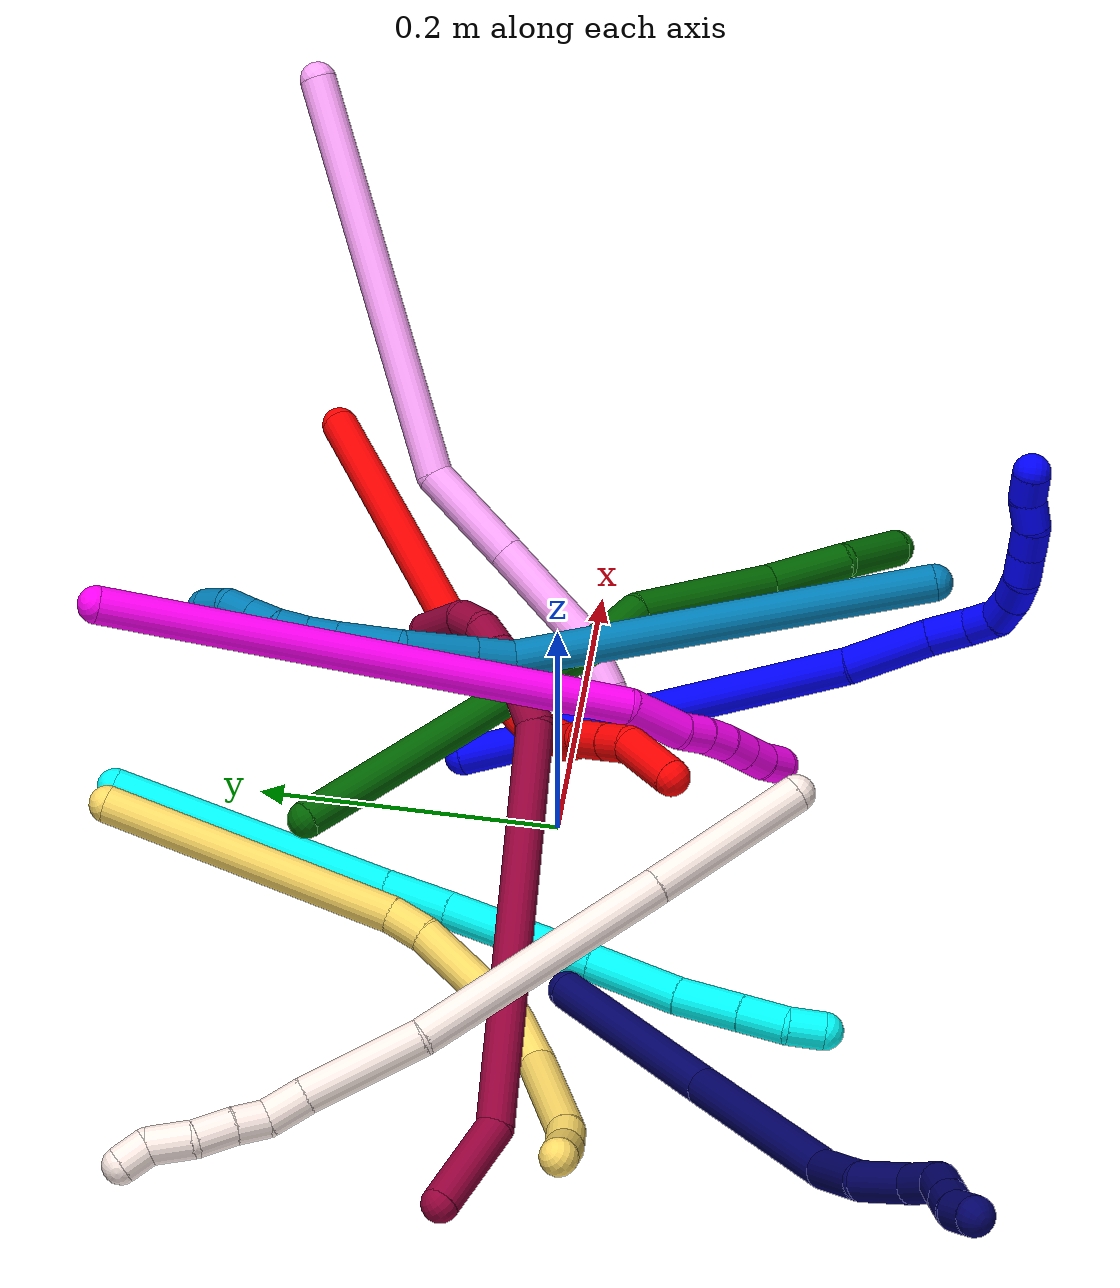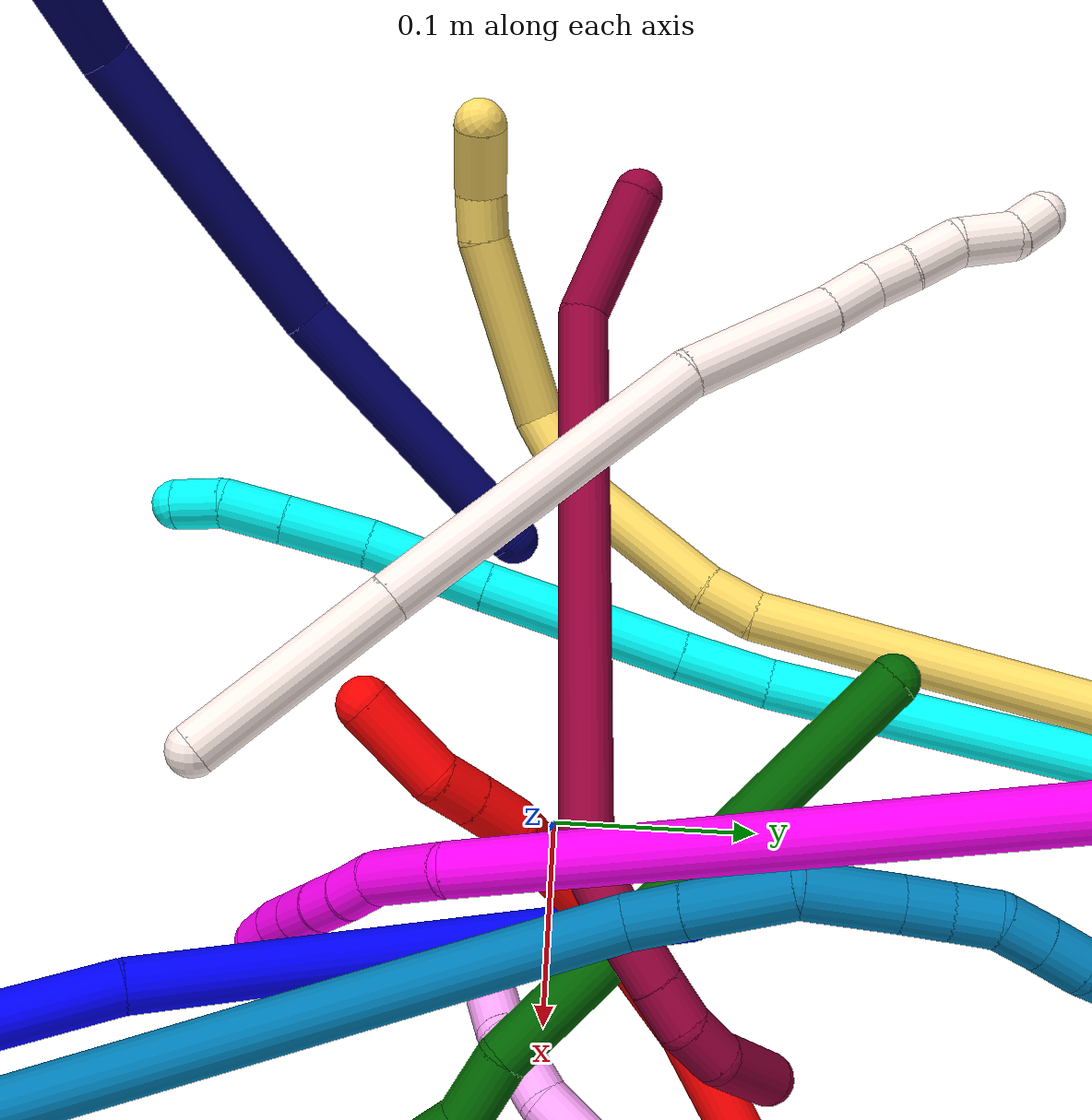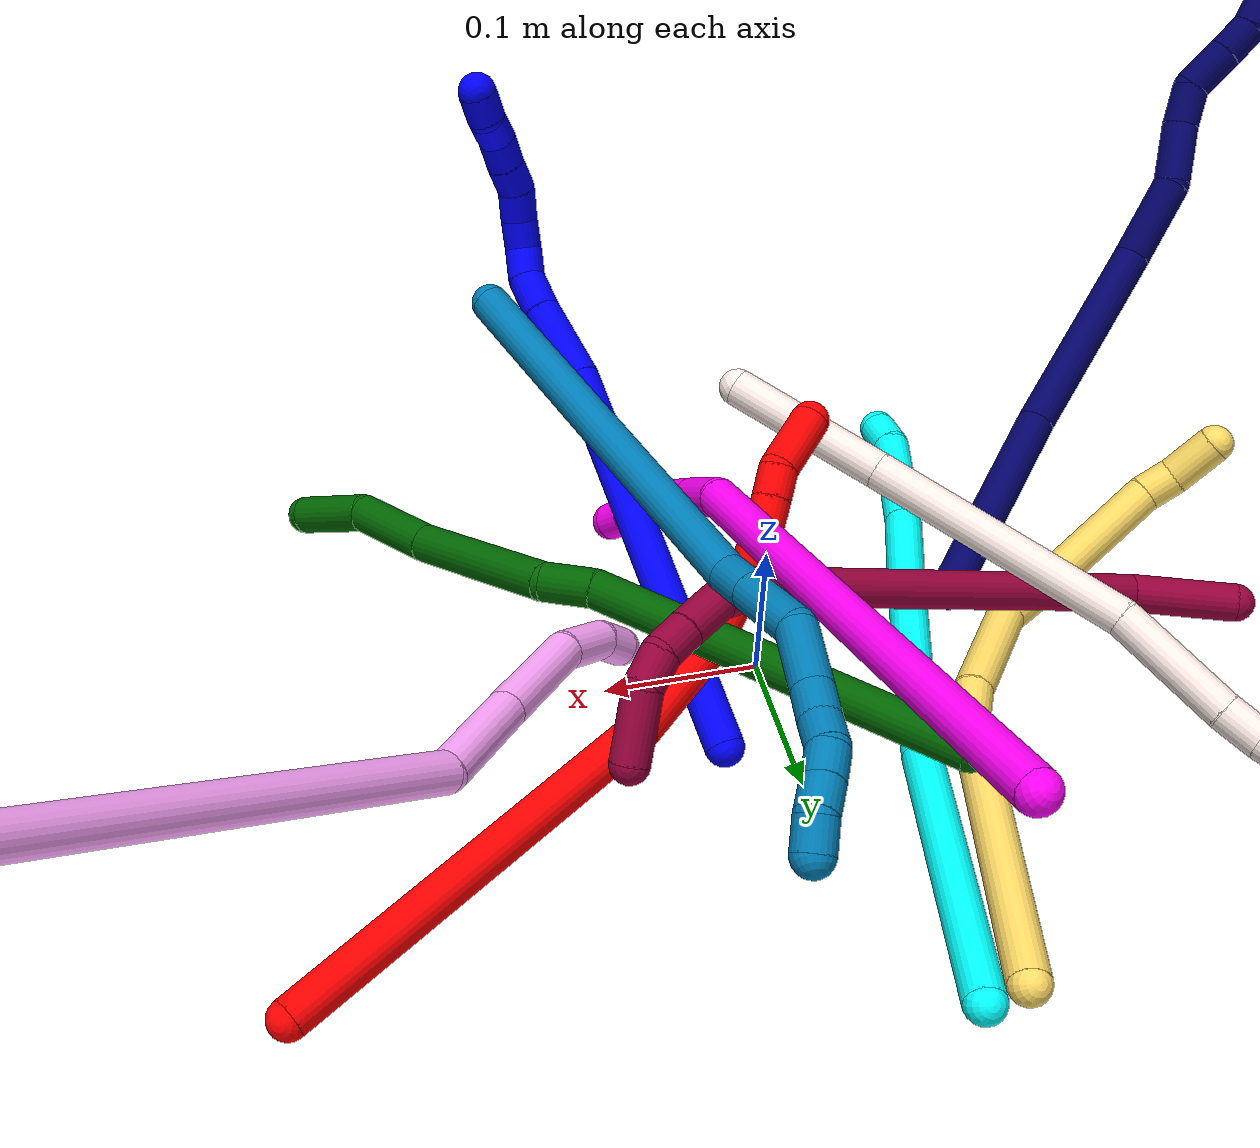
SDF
<sdf version="1.7">
 <world name="default">
  <plugin name="TubeGeneratorPlugin" filename="libtube_generator_plugin.so"/>
  <model name="photoneo_s_sensor">
   <static>1</static>
   <pose>0 0 2 1.57079 1.57079 3.14159</pose>
   <link name="link">
    <inertial><mass>0.1</mass></inertial>
    <sensor name="sensor" type="depth">
     <update_rate>30</update_rate>
     <camera>
      <horizontal_fov>1.22</horizontal_fov>
      <image><width>1920</width><height>1200</height><format>B8G8R8</format></image>
      <clip><near>0.1</near><far>4</far></clip>
      <depth_camera><output>points</output></depth_camera>
     </camera>
     <plugin name="camera_plugin" filename="libgazebo_ros_depth_camera.so">
      <baseline>0.2</baseline>
      <alwaysOn>1</alwaysOn>
      <updateRate>0.0</updateRate>
      <cameraName>camera_ir</cameraName>
      <imageTopicName>/camera/color/image_raw</imageTopicName>
      <cameraInfoTopicName>/camera/color/camera_info</cameraInfoTopicName>
      <depthImageTopicName>/camera/depth/image_raw</depthImageTopicName>
      <depthImageCameraInfoTopicName>/camera/depth/camera_info</depthImageCameraInfoTopicName>
      <pointCloudTopicName>/camera/depth/points</pointCloudTopicName>
      <frameName>fr_optical</frameName>
      <pointCloudCutoff>0.1</pointCloudCutoff>
      <pointCloudCutoffMax>2.0</pointCloudCutoffMax>
      <distortionK1>0</distortionK1>
      <distortionK2>0</distortionK2>
      <distortionK3>0</distortionK3>
      <distortionT1>0</distortionT1>
      <distortionT2>0</distortionT2>
      <CxPrime>0</CxPrime>
      <Cx>0</Cx>
      <Cy>0</Cy>
      <focalLength>0</focalLength>
      <hackBaseline>0</hackBaseline>
     </plugin>
    </sensor>
   </link>
  </model>
  <gravity>0 0 -9.8</gravity>
  <magnetic_field>6e-06 2.3e-05 -4.2e-05</magnetic_field>
  <atmosphere type="adiabatic"/>
  <physics name="default_physics" default="0" type="ode">
   <max_step_size>0.003</max_step_size>
   <real_time_factor>1</real_time_factor>
   <real_time_update_rate>1000</real_time_update_rate>
   <max_contacts>10000</max_contacts>
   <ode>
    <solver>
     <type>quick</type>
     <iters>100</iters>
     <sor>1.3</sor>
     <use_dynamic_moi_rescaling>0</use_dynamic_moi_rescaling>
    </solver>
    <constraints>
     <contact_max_correcting_vel>0</contact_max_correcting_vel>
     <contact_surface_layer>0.001</contact_surface_layer>
     <cfm>0</cfm>
     <erp>0.2</erp>
    </constraints>
   </ode>
  </physics>
  <scene><ambient>0.4 0.4 0.4 1</ambient><background>0.7 0.7 0.7 1</background><shadows>0</shadows></scene>
  <audio><device>default</device></audio>
  <spherical_coordinates>
   <surface_model>EARTH_WGS84</surface_model>
   <latitude_deg>0</latitude_deg>
   <longitude_deg>0</longitude_deg>
   <elevation>0</elevation>
   <heading_deg>0</heading_deg>
  </spherical_coordinates>
  <model name="bin">
   <static>1</static>
   <link name="bottom">
    <collision name="collision-bottom">
     <pose>0 0 -0.01 0 -0 0</pose>
     <geometry><box><size>0.8 0.6 0.02</size></box></geometry>
     <surface>
      <friction><ode><mu>100</mu><mu2>100</mu2></ode></friction>
      <contact><collide_bitmask>65535</collide_bitmask></contact>
     </surface>
    </collision>
   </link>
   <link name="west_wall">
    <collision name="collision-west_wall">
     <pose>-0.41 0 0.1 0 -0 0</pose>
     <geometry><box><size>0.02 0.6 0.2</size></box></geometry>
     <surface>
      <friction><ode><mu>100</mu><mu2>100</mu2></ode></friction>
      <contact><collide_bitmask>65535</collide_bitmask></contact>
     </surface>
    </collision>
   </link>
   <link name="east_wall">
    <collision name="collision-east_wall">
     <pose>0.41 0 0.1 0 -0 0</pose>
     <geometry><box><size>0.02 0.6 0.2</size></box></geometry>
     <surface>
      <friction><ode><mu>100</mu><mu2>100</mu2></ode></friction>
      <contact><collide_bitmask>65535</collide_bitmask></contact>
     </surface>
    </collision>
   </link>
   <link name="south_wall">
    <collision name="collision-south_wall">
     <pose>0 -0.31 0.1 0 -0 0</pose>
     <geometry><box><size>0.8 0.02 0.2</size></box></geometry>
     <surface>
      <friction><ode><mu>100</mu><mu2>100</mu2></ode></friction>
      <contact><collide_bitmask>65535</collide_bitmask></contact>
     </surface>
    </collision>
   </link>
   <link name="north_wall">
    <collision name="collision-north_wall">
     <pose>0 0.31 0.1 0 -0 0</pose>
     <geometry><box><size>0.8 0.02 0.2</size></box></geometry>
     <surface>
      <friction><ode><mu>100</mu><mu2>100</mu2></ode></friction>
      <contact><collide_bitmask>65535</collide_bitmask></contact>
     </surface>
    </collision>
   </link>
  </model>
  <model name="1">
   <static>0</static>
   <link name="1">
    <collision name="collision-cylinder-e_1_1_4">
     <pose>0.005878 -0.070791 0.115416 0.550181 0.043387 0.012248</pose>
     <geometry><cylinder><radius>0.0125</radius><length>0.271048</length></cylinder></geometry>
     <surface>
      <friction><ode><mu>1.16</mu><mu2>1.16</mu2><slip1>0</slip1><slip2>0</slip2></ode></friction>
      <contact><ode><kp>1e+06</kp><kd>1</kd><max_vel>0</max_vel><min_depth>0.001</min_depth></ode></contact>
     </surface>
    </collision>
    <visual name="visual-cylinder-e_1_1_4">
     <pose>0.005878 -0.070791 0.115416 0.550181 0.043387 0.012248</pose>
     <geometry><cylinder><radius>0.0125</radius><length>0.271048</length></cylinder></geometry>
     <material><ambient>0 0 1 1</ambient></material>
    </visual>
    <collision name="collision-cylinder-e_2_4_5">
     <pose>0.008923 -0.156634 0.254653 0.563527 -0.100219 -0.029032</pose>
     <geometry><cylinder><radius>0.0125</radius><length>0.05664</length></cylinder></geometry>
     <surface>
      <friction><ode><mu>1.16</mu><mu2>1.16</mu2><slip1>0</slip1><slip2>0</slip2></ode></friction>
      <contact><ode><kp>1e+06</kp><kd>1</kd><max_vel>0</max_vel><min_depth>0.001</min_depth></ode></contact>
     </surface>
    </collision>
    <visual name="visual-cylinder-e_2_4_5">
     <pose>0.008923 -0.156634 0.254653 0.563527 -0.100219 -0.029032</pose>
     <geometry><cylinder><radius>0.0125</radius><length>0.05664</length></cylinder></geometry>
     <material><ambient>0 0 1 1</ambient></material>
    </visual>
    <collision name="collision-cylinder-e_3_5_6">
     <pose>0.005864 -0.178736 0.290444 0.532309 -0.016178 -0.004411</pose>
     <geometry><cylinder><radius>0.0125</radius><length>0.027787</length></cylinder></geometry>
     <surface>
      <friction><ode><mu>1.16</mu><mu2>1.16</mu2><slip1>0</slip1><slip2>0</slip2></ode></friction>
      <contact><ode><kp>1e+06</kp><kd>1</kd><max_vel>0</max_vel><min_depth>0.001</min_depth></ode></contact>
     </surface>
    </collision>
    <visual name="visual-cylinder-e_3_5_6">
     <pose>0.005864 -0.178736 0.290444 0.532309 -0.016178 -0.004411</pose>
     <geometry><cylinder><radius>0.0125</radius><length>0.027787</length></cylinder></geometry>
     <material><ambient>0 0 1 1</ambient></material>
    </visual>
    <collision name="collision-cylinder-e_4_6_7">
     <pose>0.008291 -0.193522 0.309705 0.814885 0.244421 0.10592</pose>
     <geometry><cylinder><radius>0.0125</radius><length>0.021911</length></cylinder></geometry>
     <surface>
      <friction><ode><mu>1.16</mu><mu2>1.16</mu2><slip1>0</slip1><slip2>0</slip2></ode></friction>
      <contact><ode><kp>1e+06</kp><kd>1</kd><max_vel>0</max_vel><min_depth>0.001</min_depth></ode></contact>
     </surface>
    </collision>
    <visual name="visual-cylinder-e_4_6_7">
     <pose>0.008291 -0.193522 0.309705 0.814885 0.244421 0.10592</pose>
     <geometry><cylinder><radius>0.0125</radius><length>0.021911</length></cylinder></geometry>
     <material><ambient>0 0 1 1</ambient></material>
    </visual>
    <collision name="collision-cylinder-e_5_7_8">
     <pose>0.012339 -0.211432 0.319487 1.3308 0.132567 0.104096</pose>
     <geometry><cylinder><radius>0.0125</radius><length>0.021137</length></cylinder></geometry>
     <surface>
      <friction><ode><mu>1.16</mu><mu2>1.16</mu2><slip1>0</slip1><slip2>0</slip2></ode></friction>
      <contact><ode><kp>1e+06</kp><kd>1</kd><max_vel>0</max_vel><min_depth>0.001</min_depth></ode></contact>
     </surface>
    </collision>
    <visual name="visual-cylinder-e_5_7_8">
     <pose>0.012339 -0.211432 0.319487 1.3308 0.132567 0.104096</pose>
     <geometry><cylinder><radius>0.0125</radius><length>0.021137</length></cylinder></geometry>
     <material><ambient>0 0 1 1</ambient></material>
    </visual>
    <collision name="collision-cylinder-e_6_8_9">
     <pose>0.015147 -0.231978 0.322417 1.52843 0.135079 0.129491</pose>
     <geometry><cylinder><radius>0.0125</radius><length>0.02095</length></cylinder></geometry>
     <surface>
      <friction><ode><mu>1.16</mu><mu2>1.16</mu2><slip1>0</slip1><slip2>0</slip2></ode></friction>
      <contact><ode><kp>1e+06</kp><kd>1</kd><max_vel>0</max_vel><min_depth>0.001</min_depth></ode></contact>
     </surface>
    </collision>
    <visual name="visual-cylinder-e_6_8_9">
     <pose>0.015147 -0.231978 0.322417 1.52843 0.135079 0.129491</pose>
     <geometry><cylinder><radius>0.0125</radius><length>0.02095</length></cylinder></geometry>
     <material><ambient>0 0 1 1</ambient></material>
    </visual>
    <collision name="collision-cylinder-e_7_9_10">
     <pose>0.014725 -0.252303 0.322275 1.62912 -0.1817 -0.192554</pose>
     <geometry><cylinder><radius>0.0125</radius><length>0.020276</length></cylinder></geometry>
     <surface>
      <friction><ode><mu>1.16</mu><mu2>1.16</mu2><slip1>0</slip1><slip2>0</slip2></ode></friction>
      <contact><ode><kp>1e+06</kp><kd>1</kd><max_vel>0</max_vel><min_depth>0.001</min_depth></ode></contact>
     </surface>
    </collision>
    <visual name="visual-cylinder-e_7_9_10">
     <pose>0.014725 -0.252303 0.322275 1.62912 -0.1817 -0.192554</pose>
     <geometry><cylinder><radius>0.0125</radius><length>0.020276</length></cylinder></geometry>
     <material><ambient>0 0 1 1</ambient></material>
    </visual>
    <collision name="collision-cylinder-e_8_10_11">
     <pose>0.011833 -0.272296 0.320922 1.64756 -0.104958 -0.113324</pose>
     <geometry><cylinder><radius>0.0125</radius><length>0.020249</length></cylinder></geometry>
     <surface>
      <friction><ode><mu>1.16</mu><mu2>1.16</mu2><slip1>0</slip1><slip2>0</slip2></ode></friction>
      <contact><ode><kp>1e+06</kp><kd>1</kd><max_vel>0</max_vel><min_depth>0.001</min_depth></ode></contact>
     </surface>
    </collision>
    <visual name="visual-cylinder-e_8_10_11">
     <pose>0.011833 -0.272296 0.320922 1.64756 -0.104958 -0.113324</pose>
     <geometry><cylinder><radius>0.0125</radius><length>0.020249</length></cylinder></geometry>
     <material><ambient>0 0 1 1</ambient></material>
    </visual>
    <collision name="collision-cylinder-e_9_11_12">
     <pose>0.008215 -0.291352 0.316663 1.9398 -0.258589 -0.374915</pose>
     <geometry><cylinder><radius>0.0125</radius><length>0.02</length></cylinder></geometry>
     <surface>
      <friction><ode><mu>1.16</mu><mu2>1.16</mu2><slip1>0</slip1><slip2>0</slip2></ode></friction>
      <contact><ode><kp>1e+06</kp><kd>1</kd><max_vel>0</max_vel><min_depth>0.001</min_depth></ode></contact>
     </surface>
    </collision>
    <visual name="visual-cylinder-e_9_11_12">
     <pose>0.008215 -0.291352 0.316663 1.9398 -0.258589 -0.374915</pose>
     <geometry><cylinder><radius>0.0125</radius><length>0.02</length></cylinder></geometry>
     <material><ambient>0 0 1 1</ambient></material>
    </visual>
    <collision name="collision-cylinder-e_10_12_2">
     <pose>0.004509 -0.310264 0.3123 1.6591 -0.115137 -0.125754</pose>
     <geometry><cylinder><radius>0.0125</radius><length>0.02</length></cylinder></geometry>
     <surface>
      <friction><ode><mu>1.16</mu><mu2>1.16</mu2><slip1>0</slip1><slip2>0</slip2></ode></friction>
      <contact><ode><kp>1e+06</kp><kd>1</kd><max_vel>0</max_vel><min_depth>0.001</min_depth></ode></contact>
     </surface>
    </collision>
    <visual name="visual-cylinder-e_10_12_2">
     <pose>0.004509 -0.310264 0.3123 1.6591 -0.115137 -0.125754</pose>
     <geometry><cylinder><radius>0.0125</radius><length>0.02</length></cylinder></geometry>
     <material><ambient>0 0 1 1</ambient></material>
    </visual>
    <collision name="collision-sphere-2">
     <pose>0.00336 -0.320159 0.311423 0 -0 0</pose>
     <geometry><sphere><radius>0.0125</radius></sphere></geometry>
     <surface>
      <friction><ode><mu>1.16</mu><mu2>1.16</mu2><slip1>0</slip1><slip2>0</slip2></ode></friction>
      <contact><ode><kp>1e+06</kp><kd>1</kd><max_vel>0</max_vel><min_depth>0.001</min_depth></ode></contact>
     </surface>
    </collision>
    <visual name="visual-sphere-2">
     <pose>0.00336 -0.320159 0.311423 0 -0 0</pose>
     <geometry><sphere><radius>0.0125</radius></sphere></geometry>
     <material><ambient>0 0 1 1</ambient></material>
    </visual>
    <collision name="collision-sphere-12">
     <pose>0.005658 -0.300369 0.313176 0 -0 0</pose>
     <geometry><sphere><radius>0.0125</radius></sphere></geometry>
     <surface>
      <friction><ode><mu>1.16</mu><mu2>1.16</mu2><slip1>0</slip1><slip2>0</slip2></ode></friction>
      <contact><ode><kp>1e+06</kp><kd>1</kd><max_vel>0</max_vel><min_depth>0.001</min_depth></ode></contact>
     </surface>
    </collision>
    <visual name="visual-sphere-12">
     <pose>0.005658 -0.300369 0.313176 0 -0 0</pose>
     <geometry><sphere><radius>0.0125</radius></sphere></geometry>
     <material><ambient>0 0 1 1</ambient></material>
    </visual>
    <collision name="collision-sphere-11">
     <pose>0.010772 -0.282335 0.32015 0 -0 0</pose>
     <geometry><sphere><radius>0.0125</radius></sphere></geometry>
     <surface>
      <friction><ode><mu>1.16</mu><mu2>1.16</mu2><slip1>0</slip1><slip2>0</slip2></ode></friction>
      <contact><ode><kp>1e+06</kp><kd>1</kd><max_vel>0</max_vel><min_depth>0.001</min_depth></ode></contact>
     </surface>
    </collision>
    <visual name="visual-sphere-11">
     <pose>0.010772 -0.282335 0.32015 0 -0 0</pose>
     <geometry><sphere><radius>0.0125</radius></sphere></geometry>
     <material><ambient>0 0 1 1</ambient></material>
    </visual>
    <collision name="collision-sphere-10">
     <pose>0.012893 -0.262257 0.321694 0 -0 0</pose>
     <geometry><sphere><radius>0.0125</radius></sphere></geometry>
     <surface>
      <friction><ode><mu>1.16</mu><mu2>1.16</mu2><slip1>0</slip1><slip2>0</slip2></ode></friction>
      <contact><ode><kp>1e+06</kp><kd>1</kd><max_vel>0</max_vel><min_depth>0.001</min_depth></ode></contact>
     </surface>
    </collision>
    <visual name="visual-sphere-10">
     <pose>0.012893 -0.262257 0.321694 0 -0 0</pose>
     <geometry><sphere><radius>0.0125</radius></sphere></geometry>
     <material><ambient>0 0 1 1</ambient></material>
    </visual>
    <collision name="collision-sphere-9">
     <pose>0.016557 -0.242348 0.322856 0 -0 0</pose>
     <geometry><sphere><radius>0.0125</radius></sphere></geometry>
     <surface>
      <friction><ode><mu>1.16</mu><mu2>1.16</mu2><slip1>0</slip1><slip2>0</slip2></ode></friction>
      <contact><ode><kp>1e+06</kp><kd>1</kd><max_vel>0</max_vel><min_depth>0.001</min_depth></ode></contact>
     </surface>
    </collision>
    <visual name="visual-sphere-9">
     <pose>0.016557 -0.242348 0.322856 0 -0 0</pose>
     <geometry><sphere><radius>0.0125</radius></sphere></geometry>
     <material><ambient>0 0 1 1</ambient></material>
    </visual>
    <collision name="collision-sphere-4">
     <pose>0.011756 -0.141582 0.230832 0 -0 0</pose>
     <geometry><sphere><radius>0.0125</radius></sphere></geometry>
     <surface>
      <friction><ode><mu>1.16</mu><mu2>1.16</mu2><slip1>0</slip1><slip2>0</slip2></ode></friction>
      <contact><ode><kp>1e+06</kp><kd>1</kd><max_vel>0</max_vel><min_depth>0.001</min_depth></ode></contact>
     </surface>
    </collision>
    <visual name="visual-sphere-4">
     <pose>0.011756 -0.141582 0.230832 0 -0 0</pose>
     <geometry><sphere><radius>0.0125</radius></sphere></geometry>
     <material><ambient>0 0 1 1</ambient></material>
    </visual>
    <collision name="collision-sphere-1">
     <geometry><sphere><radius>0.0125</radius></sphere></geometry>
     <surface>
      <friction><ode><mu>1.16</mu><mu2>1.16</mu2><slip1>0</slip1><slip2>0</slip2></ode></friction>
      <contact><ode><kp>1e+06</kp><kd>1</kd><max_vel>0</max_vel><min_depth>0.001</min_depth></ode></contact>
     </surface>
    </collision>
    <visual name="visual-sphere-1">
     <geometry><sphere><radius>0.0125</radius></sphere></geometry>
     <material><ambient>0 0 1 1</ambient></material>
    </visual>
    <collision name="collision-sphere-8">
     <pose>0.013736 -0.221608 0.321977 0 -0 0</pose>
     <geometry><sphere><radius>0.0125</radius></sphere></geometry>
     <surface>
      <friction><ode><mu>1.16</mu><mu2>1.16</mu2><slip1>0</slip1><slip2>0</slip2></ode></friction>
      <contact><ode><kp>1e+06</kp><kd>1</kd><max_vel>0</max_vel><min_depth>0.001</min_depth></ode></contact>
     </surface>
    </collision>
    <visual name="visual-sphere-8">
     <pose>0.013736 -0.221608 0.321977 0 -0 0</pose>
     <geometry><sphere><radius>0.0125</radius></sphere></geometry>
     <material><ambient>0 0 1 1</ambient></material>
    </visual>
    <collision name="collision-sphere-5">
     <pose>0.006089 -0.171686 0.278474 0 -0 0</pose>
     <geometry><sphere><radius>0.0125</radius></sphere></geometry>
     <surface>
      <friction><ode><mu>1.16</mu><mu2>1.16</mu2><slip1>0</slip1><slip2>0</slip2></ode></friction>
      <contact><ode><kp>1e+06</kp><kd>1</kd><max_vel>0</max_vel><min_depth>0.001</min_depth></ode></contact>
     </surface>
    </collision>
    <visual name="visual-sphere-5">
     <pose>0.006089 -0.171686 0.278474 0 -0 0</pose>
     <geometry><sphere><radius>0.0125</radius></sphere></geometry>
     <material><ambient>0 0 1 1</ambient></material>
    </visual>
    <collision name="collision-sphere-6">
     <pose>0.00564 -0.185787 0.302414 0 -0 0</pose>
     <geometry><sphere><radius>0.0125</radius></sphere></geometry>
     <surface>
      <friction><ode><mu>1.16</mu><mu2>1.16</mu2><slip1>0</slip1><slip2>0</slip2></ode></friction>
      <contact><ode><kp>1e+06</kp><kd>1</kd><max_vel>0</max_vel><min_depth>0.001</min_depth></ode></contact>
     </surface>
    </collision>
    <visual name="visual-sphere-6">
     <pose>0.00564 -0.185787 0.302414 0 -0 0</pose>
     <geometry><sphere><radius>0.0125</radius></sphere></geometry>
     <material><ambient>0 0 1 1</ambient></material>
    </visual>
    <collision name="collision-sphere-7">
     <pose>0.010942 -0.201256 0.316997 0 -0 0</pose>
     <geometry><sphere><radius>0.0125</radius></sphere></geometry>
     <surface>
      <friction><ode><mu>1.16</mu><mu2>1.16</mu2><slip1>0</slip1><slip2>0</slip2></ode></friction>
      <contact><ode><kp>1e+06</kp><kd>1</kd><max_vel>0</max_vel><min_depth>0.001</min_depth></ode></contact>
     </surface>
    </collision>
    <visual name="visual-sphere-7">
     <pose>0.010942 -0.201256 0.316997 0 -0 0</pose>
     <geometry><sphere><radius>0.0125</radius></sphere></geometry>
     <material><ambient>0 0 1 1</ambient></material>
    </visual>
    <inertial>
     <pose>0.007628 -0.138515 0.199367 0 -0 0</pose>
     <mass>0.5</mass>
     <inertia>
      <ixx>0.001718</ixx>
      <ixy>0</ixy>
      <ixz>0</ixz>
      <iyy>0.001437</iyy>
      <iyz>0</iyz>
      <izz>0.000847</izz>
     </inertia>
    </inertial>
   </link>
   <pose>0.041094 0.070093 0.011469 -1.7515 -0.133 -3.00849</pose>
  </model>
  <model name="2">
   <static>0</static>
   <link name="2">
    <collision name="collision-cylinder-e_1_1_4">
     <pose>-0.092179 -0.034334 -0.089189 2.77412 -0.767345 -2.27874</pose>
     <geometry><cylinder><radius>0.0125</radius><length>0.265559</length></cylinder></geometry>
     <surface>
      <friction><ode><mu>1.16</mu><mu2>1.16</mu2><slip1>0</slip1><slip2>0</slip2></ode></friction>
      <contact><ode><kp>1e+06</kp><kd>1</kd><max_vel>0</max_vel><min_depth>0.001</min_depth></ode></contact>
     </surface>
    </collision>
    <visual name="visual-cylinder-e_1_1_4">
     <pose>-0.092179 -0.034334 -0.089189 2.77412 -0.767345 -2.27874</pose>
     <geometry><cylinder><radius>0.0125</radius><length>0.265559</length></cylinder></geometry>
     <material><ambient>1 0 0 1</ambient></material>
    </visual>
    <collision name="collision-cylinder-e_2_4_5">
     <pose>-0.208057 -0.084374 -0.200339 2.52075 -0.720374 -1.73054</pose>
     <geometry><cylinder><radius>0.0125</radius><length>0.071852</length></cylinder></geometry>
     <surface>
      <friction><ode><mu>1.16</mu><mu2>1.16</mu2><slip1>0</slip1><slip2>0</slip2></ode></friction>
      <contact><ode><kp>1e+06</kp><kd>1</kd><max_vel>0</max_vel><min_depth>0.001</min_depth></ode></contact>
     </surface>
    </collision>
    <visual name="visual-cylinder-e_2_4_5">
     <pose>-0.208057 -0.084374 -0.200339 2.52075 -0.720374 -1.73054</pose>
     <geometry><cylinder><radius>0.0125</radius><length>0.071852</length></cylinder></geometry>
     <material><ambient>1 0 0 1</ambient></material>
    </visual>
    <collision name="collision-cylinder-e_3_5_6">
     <pose>-0.246376 -0.114953 -0.23211 2.15386 -0.687191 -1.17312</pose>
     <geometry><cylinder><radius>0.0125</radius><length>0.046093</length></cylinder></geometry>
     <surface>
      <friction><ode><mu>1.16</mu><mu2>1.16</mu2><slip1>0</slip1><slip2>0</slip2></ode></friction>
      <contact><ode><kp>1e+06</kp><kd>1</kd><max_vel>0</max_vel><min_depth>0.001</min_depth></ode></contact>
     </surface>
    </collision>
    <visual name="visual-cylinder-e_3_5_6">
     <pose>-0.246376 -0.114953 -0.23211 2.15386 -0.687191 -1.17312</pose>
     <geometry><cylinder><radius>0.0125</radius><length>0.046093</length></cylinder></geometry>
     <material><ambient>1 0 0 1</ambient></material>
    </visual>
    <collision name="collision-cylinder-e_4_6_7">
     <pose>-0.270446 -0.139528 -0.242263 1.60631 -0.771889 -0.796977</pose>
     <geometry><cylinder><radius>0.0125</radius><length>0.027097</length></cylinder></geometry>
     <surface>
      <friction><ode><mu>1.16</mu><mu2>1.16</mu2><slip1>0</slip1><slip2>0</slip2></ode></friction>
      <contact><ode><kp>1e+06</kp><kd>1</kd><max_vel>0</max_vel><min_depth>0.001</min_depth></ode></contact>
     </surface>
    </collision>
    <visual name="visual-cylinder-e_4_6_7">
     <pose>-0.270446 -0.139528 -0.242263 1.60631 -0.771889 -0.796977</pose>
     <geometry><cylinder><radius>0.0125</radius><length>0.027097</length></cylinder></geometry>
     <material><ambient>1 0 0 1</ambient></material>
    </visual>
    <collision name="collision-cylinder-e_5_7_8">
     <pose>-0.286228 -0.159301 -0.24726 2.0035 -0.518674 -0.786387</pose>
     <geometry><cylinder><radius>0.0125</radius><length>0.025545</length></cylinder></geometry>
     <surface>
      <friction><ode><mu>1.16</mu><mu2>1.16</mu2><slip1>0</slip1><slip2>0</slip2></ode></friction>
      <contact><ode><kp>1e+06</kp><kd>1</kd><max_vel>0</max_vel><min_depth>0.001</min_depth></ode></contact>
     </surface>
    </collision>
    <visual name="visual-cylinder-e_5_7_8">
     <pose>-0.286228 -0.159301 -0.24726 2.0035 -0.518674 -0.786387</pose>
     <geometry><cylinder><radius>0.0125</radius><length>0.025545</length></cylinder></geometry>
     <material><ambient>1 0 0 1</ambient></material>
    </visual>
    <collision name="collision-cylinder-e_6_8_9">
     <pose>-0.297498 -0.177564 -0.255695 2.00347 -0.500695 -0.760617</pose>
     <geometry><cylinder><radius>0.0125</radius><length>0.020573</length></cylinder></geometry>
     <surface>
      <friction><ode><mu>1.16</mu><mu2>1.16</mu2><slip1>0</slip1><slip2>0</slip2></ode></friction>
      <contact><ode><kp>1e+06</kp><kd>1</kd><max_vel>0</max_vel><min_depth>0.001</min_depth></ode></contact>
     </surface>
    </collision>
    <visual name="visual-cylinder-e_6_8_9">
     <pose>-0.297498 -0.177564 -0.255695 2.00347 -0.500695 -0.760617</pose>
     <geometry><cylinder><radius>0.0125</radius><length>0.020573</length></cylinder></geometry>
     <material><ambient>1 0 0 1</ambient></material>
    </visual>
    <collision name="collision-cylinder-e_7_9_2">
     <pose>-0.314195 -0.196668 -0.274003 2.4973 -0.574465 -1.44897</pose>
     <geometry><cylinder><radius>0.0125</radius><length>0.043281</length></cylinder></geometry>
     <surface>
      <friction><ode><mu>1.16</mu><mu2>1.16</mu2><slip1>0</slip1><slip2>0</slip2></ode></friction>
      <contact><ode><kp>1e+06</kp><kd>1</kd><max_vel>0</max_vel><min_depth>0.001</min_depth></ode></contact>
     </surface>
    </collision>
    <visual name="visual-cylinder-e_7_9_2">
     <pose>-0.314195 -0.196668 -0.274003 2.4973 -0.574465 -1.44897</pose>
     <geometry><cylinder><radius>0.0125</radius><length>0.043281</length></cylinder></geometry>
     <material><ambient>1 0 0 1</ambient></material>
    </visual>
    <collision name="collision-sphere-2">
     <pose>-0.325954 -0.207579 -0.288528 0 -0 0</pose>
     <geometry><sphere><radius>0.0125</radius></sphere></geometry>
     <surface>
      <friction><ode><mu>1.16</mu><mu2>1.16</mu2><slip1>0</slip1><slip2>0</slip2></ode></friction>
      <contact><ode><kp>1e+06</kp><kd>1</kd><max_vel>0</max_vel><min_depth>0.001</min_depth></ode></contact>
     </surface>
    </collision>
    <visual name="visual-sphere-2">
     <pose>-0.325954 -0.207579 -0.288528 0 -0 0</pose>
     <geometry><sphere><radius>0.0125</radius></sphere></geometry>
     <material><ambient>1 0 0 1</ambient></material>
    </visual>
    <collision name="collision-sphere-9">
     <pose>-0.302436 -0.185756 -0.259478 0 -0 0</pose>
     <geometry><sphere><radius>0.0125</radius></sphere></geometry>
     <surface>
      <friction><ode><mu>1.16</mu><mu2>1.16</mu2><slip1>0</slip1><slip2>0</slip2></ode></friction>
      <contact><ode><kp>1e+06</kp><kd>1</kd><max_vel>0</max_vel><min_depth>0.001</min_depth></ode></contact>
     </surface>
    </collision>
    <visual name="visual-sphere-9">
     <pose>-0.302436 -0.185756 -0.259478 0 -0 0</pose>
     <geometry><sphere><radius>0.0125</radius></sphere></geometry>
     <material><ambient>1 0 0 1</ambient></material>
    </visual>
    <collision name="collision-sphere-4">
     <pose>-0.184358 -0.068667 -0.178377 0 -0 0</pose>
     <geometry><sphere><radius>0.0125</radius></sphere></geometry>
     <surface>
      <friction><ode><mu>1.16</mu><mu2>1.16</mu2><slip1>0</slip1><slip2>0</slip2></ode></friction>
      <contact><ode><kp>1e+06</kp><kd>1</kd><max_vel>0</max_vel><min_depth>0.001</min_depth></ode></contact>
     </surface>
    </collision>
    <visual name="visual-sphere-4">
     <pose>-0.184358 -0.068667 -0.178377 0 -0 0</pose>
     <geometry><sphere><radius>0.0125</radius></sphere></geometry>
     <material><ambient>1 0 0 1</ambient></material>
    </visual>
    <collision name="collision-sphere-1">
     <geometry><sphere><radius>0.0125</radius></sphere></geometry>
     <surface>
      <friction><ode><mu>1.16</mu><mu2>1.16</mu2><slip1>0</slip1><slip2>0</slip2></ode></friction>
      <contact><ode><kp>1e+06</kp><kd>1</kd><max_vel>0</max_vel><min_depth>0.001</min_depth></ode></contact>
     </surface>
    </collision>
    <visual name="visual-sphere-1">
     <geometry><sphere><radius>0.0125</radius></sphere></geometry>
     <material><ambient>1 0 0 1</ambient></material>
    </visual>
    <collision name="collision-sphere-8">
     <pose>-0.29256 -0.169371 -0.251911 0 -0 0</pose>
     <geometry><sphere><radius>0.0125</radius></sphere></geometry>
     <surface>
      <friction><ode><mu>1.16</mu><mu2>1.16</mu2><slip1>0</slip1><slip2>0</slip2></ode></friction>
      <contact><ode><kp>1e+06</kp><kd>1</kd><max_vel>0</max_vel><min_depth>0.001</min_depth></ode></contact>
     </surface>
    </collision>
    <visual name="visual-sphere-8">
     <pose>-0.29256 -0.169371 -0.251911 0 -0 0</pose>
     <geometry><sphere><radius>0.0125</radius></sphere></geometry>
     <material><ambient>1 0 0 1</ambient></material>
    </visual>
    <collision name="collision-sphere-5">
     <pose>-0.231757 -0.100081 -0.222301 0 -0 0</pose>
     <geometry><sphere><radius>0.0125</radius></sphere></geometry>
     <surface>
      <friction><ode><mu>1.16</mu><mu2>1.16</mu2><slip1>0</slip1><slip2>0</slip2></ode></friction>
      <contact><ode><kp>1e+06</kp><kd>1</kd><max_vel>0</max_vel><min_depth>0.001</min_depth></ode></contact>
     </surface>
    </collision>
    <visual name="visual-sphere-5">
     <pose>-0.231757 -0.100081 -0.222301 0 -0 0</pose>
     <geometry><sphere><radius>0.0125</radius></sphere></geometry>
     <material><ambient>1 0 0 1</ambient></material>
    </visual>
    <collision name="collision-sphere-6">
     <pose>-0.260996 -0.129825 -0.241919 0 -0 0</pose>
     <geometry><sphere><radius>0.0125</radius></sphere></geometry>
     <surface>
      <friction><ode><mu>1.16</mu><mu2>1.16</mu2><slip1>0</slip1><slip2>0</slip2></ode></friction>
      <contact><ode><kp>1e+06</kp><kd>1</kd><max_vel>0</max_vel><min_depth>0.001</min_depth></ode></contact>
     </surface>
    </collision>
    <visual name="visual-sphere-6">
     <pose>-0.260996 -0.129825 -0.241919 0 -0 0</pose>
     <geometry><sphere><radius>0.0125</radius></sphere></geometry>
     <material><ambient>1 0 0 1</ambient></material>
    </visual>
    <collision name="collision-sphere-7">
     <pose>-0.279896 -0.149231 -0.242608 0 -0 0</pose>
     <geometry><sphere><radius>0.0125</radius></sphere></geometry>
     <surface>
      <friction><ode><mu>1.16</mu><mu2>1.16</mu2><slip1>0</slip1><slip2>0</slip2></ode></friction>
      <contact><ode><kp>1e+06</kp><kd>1</kd><max_vel>0</max_vel><min_depth>0.001</min_depth></ode></contact>
     </surface>
    </collision>
    <visual name="visual-sphere-7">
     <pose>-0.279896 -0.149231 -0.242608 0 -0 0</pose>
     <geometry><sphere><radius>0.0125</radius></sphere></geometry>
     <material><ambient>1 0 0 1</ambient></material>
    </visual>
    <inertial>
     <pose>-0.170287 -0.080988 -0.157557 0 -0 0</pose>
     <mass>0.5</mass>
     <inertia>
      <ixx>-0.001659</ixx>
      <ixy>0</ixy>
      <ixz>0</ixz>
      <iyy>0.000356</iyy>
      <iyz>0</iyz>
      <izz>0.001542</izz>
     </inertia>
    </inertial>
   </link>
   <pose>0.320763 0.203291 0.011963 -0.83595 0.490634 -0.203249</pose>
  </model>
  <model name="3">
   <static>0</static>
   <link name="3">
    <collision name="collision-cylinder-e_1_1_4">
     <pose>-0.016214 -0.063018 -0.070031 2.40885 -0.170433 -0.438123</pose>
     <geometry><cylinder><radius>0.0125</radius><length>0.191191</length></cylinder></geometry>
     <surface>
      <friction><ode><mu>1.16</mu><mu2>1.16</mu2><slip1>0</slip1><slip2>0</slip2></ode></friction>
      <contact><ode><kp>1e+06</kp><kd>1</kd><max_vel>0</max_vel><min_depth>0.001</min_depth></ode></contact>
     </surface>
    </collision>
    <visual name="visual-cylinder-e_1_1_4">
     <pose>-0.016214 -0.063018 -0.070031 2.40885 -0.170433 -0.438123</pose>
     <geometry><cylinder><radius>0.0125</radius><length>0.191191</length></cylinder></geometry>
     <material><ambient>0.003922 1 0.996078 1</ambient></material>
    </visual>
    <collision name="collision-cylinder-e_2_4_5">
     <pose>-0.037588 -0.143071 -0.154335 2.26822 -0.228159 -0.481448</pose>
     <geometry><cylinder><radius>0.0125</radius><length>0.04563</length></cylinder></geometry>
     <surface>
      <friction><ode><mu>1.16</mu><mu2>1.16</mu2><slip1>0</slip1><slip2>0</slip2></ode></friction>
      <contact><ode><kp>1e+06</kp><kd>1</kd><max_vel>0</max_vel><min_depth>0.001</min_depth></ode></contact>
     </surface>
    </collision>
    <visual name="visual-cylinder-e_2_4_5">
     <pose>-0.037588 -0.143071 -0.154335 2.26822 -0.228159 -0.481448</pose>
     <geometry><cylinder><radius>0.0125</radius><length>0.04563</length></cylinder></geometry>
     <material><ambient>0.003922 1 0.996078 1</ambient></material>
    </visual>
    <collision name="collision-cylinder-e_3_5_6">
     <pose>-0.055653 -0.19859 -0.199773 2.25149 -0.254924 -0.524983</pose>
     <geometry><cylinder><radius>0.0125</radius><length>0.102349</length></cylinder></geometry>
     <surface>
      <friction><ode><mu>1.16</mu><mu2>1.16</mu2><slip1>0</slip1><slip2>0</slip2></ode></friction>
      <contact><ode><kp>1e+06</kp><kd>1</kd><max_vel>0</max_vel><min_depth>0.001</min_depth></ode></contact>
     </surface>
    </collision>
    <visual name="visual-cylinder-e_3_5_6">
     <pose>-0.055653 -0.19859 -0.199773 2.25149 -0.254924 -0.524983</pose>
     <geometry><cylinder><radius>0.0125</radius><length>0.102349</length></cylinder></geometry>
     <material><ambient>0.003922 1 0.996078 1</ambient></material>
    </visual>
    <collision name="collision-cylinder-e_4_6_7">
     <pose>-0.076922 -0.260198 -0.249716 2.25285 -0.273738 -0.563168</pose>
     <geometry><cylinder><radius>0.0125</radius><length>0.061879</length></cylinder></geometry>
     <surface>
      <friction><ode><mu>1.16</mu><mu2>1.16</mu2><slip1>0</slip1><slip2>0</slip2></ode></friction>
      <contact><ode><kp>1e+06</kp><kd>1</kd><max_vel>0</max_vel><min_depth>0.001</min_depth></ode></contact>
     </surface>
    </collision>
    <visual name="visual-cylinder-e_4_6_7">
     <pose>-0.076922 -0.260198 -0.249716 2.25285 -0.273738 -0.563168</pose>
     <geometry><cylinder><radius>0.0125</radius><length>0.061879</length></cylinder></geometry>
     <material><ambient>0.003922 1 0.996078 1</ambient></material>
    </visual>
    <collision name="collision-cylinder-e_5_7_8">
     <pose>-0.089291 -0.300574 -0.281121 2.20261 -0.185176 -0.362044</pose>
     <geometry><cylinder><radius>0.0125</radius><length>0.043504</length></cylinder></geometry>
     <surface>
      <friction><ode><mu>1.16</mu><mu2>1.16</mu2><slip1>0</slip1><slip2>0</slip2></ode></friction>
      <contact><ode><kp>1e+06</kp><kd>1</kd><max_vel>0</max_vel><min_depth>0.001</min_depth></ode></contact>
     </surface>
    </collision>
    <visual name="visual-cylinder-e_5_7_8">
     <pose>-0.089291 -0.300574 -0.281121 2.20261 -0.185176 -0.362044</pose>
     <geometry><cylinder><radius>0.0125</radius><length>0.043504</length></cylinder></geometry>
     <material><ambient>0.003922 1 0.996078 1</ambient></material>
    </visual>
    <collision name="collision-cylinder-e_6_8_9">
     <pose>-0.096089 -0.330183 -0.30308 2.21764 -0.178456 -0.355566</pose>
     <geometry><cylinder><radius>0.0125</radius><length>0.031467</length></cylinder></geometry>
     <surface>
      <friction><ode><mu>1.16</mu><mu2>1.16</mu2><slip1>0</slip1><slip2>0</slip2></ode></friction>
      <contact><ode><kp>1e+06</kp><kd>1</kd><max_vel>0</max_vel><min_depth>0.001</min_depth></ode></contact>
     </surface>
    </collision>
    <visual name="visual-cylinder-e_6_8_9">
     <pose>-0.096089 -0.330183 -0.30308 2.21764 -0.178456 -0.355566</pose>
     <geometry><cylinder><radius>0.0125</radius><length>0.031467</length></cylinder></geometry>
     <material><ambient>0.003922 1 0.996078 1</ambient></material>
    </visual>
    <collision name="collision-cylinder-e_7_9_2">
     <pose>-0.097892 -0.350549 -0.321277 2.40683 0.082597 0.213921</pose>
     <geometry><cylinder><radius>0.0125</radius><length>0.02398</length></cylinder></geometry>
     <surface>
      <friction><ode><mu>1.16</mu><mu2>1.16</mu2><slip1>0</slip1><slip2>0</slip2></ode></friction>
      <contact><ode><kp>1e+06</kp><kd>1</kd><max_vel>0</max_vel><min_depth>0.001</min_depth></ode></contact>
     </surface>
    </collision>
    <visual name="visual-cylinder-e_7_9_2">
     <pose>-0.097892 -0.350549 -0.321277 2.40683 0.082597 0.213921</pose>
     <geometry><cylinder><radius>0.0125</radius><length>0.02398</length></cylinder></geometry>
     <material><ambient>0.003922 1 0.996078 1</ambient></material>
    </visual>
    <collision name="collision-sphere-2">
     <pose>-0.096903 -0.35856 -0.330143 0 -0 0</pose>
     <geometry><sphere><radius>0.0125</radius></sphere></geometry>
     <surface>
      <friction><ode><mu>1.16</mu><mu2>1.16</mu2><slip1>0</slip1><slip2>0</slip2></ode></friction>
      <contact><ode><kp>1e+06</kp><kd>1</kd><max_vel>0</max_vel><min_depth>0.001</min_depth></ode></contact>
     </surface>
    </collision>
    <visual name="visual-sphere-2">
     <pose>-0.096903 -0.35856 -0.330143 0 -0 0</pose>
     <geometry><sphere><radius>0.0125</radius></sphere></geometry>
     <material><ambient>0.003922 1 0.996078 1</ambient></material>
    </visual>
    <collision name="collision-sphere-9">
     <pose>-0.098882 -0.342538 -0.312411 0 -0 0</pose>
     <geometry><sphere><radius>0.0125</radius></sphere></geometry>
     <surface>
      <friction><ode><mu>1.16</mu><mu2>1.16</mu2><slip1>0</slip1><slip2>0</slip2></ode></friction>
      <contact><ode><kp>1e+06</kp><kd>1</kd><max_vel>0</max_vel><min_depth>0.001</min_depth></ode></contact>
     </surface>
    </collision>
    <visual name="visual-sphere-9">
     <pose>-0.098882 -0.342538 -0.312411 0 -0 0</pose>
     <geometry><sphere><radius>0.0125</radius></sphere></geometry>
     <material><ambient>0.003922 1 0.996078 1</ambient></material>
    </visual>
    <collision name="collision-sphere-4">
     <pose>-0.032428 -0.126037 -0.140062 0 -0 0</pose>
     <geometry><sphere><radius>0.0125</radius></sphere></geometry>
     <surface>
      <friction><ode><mu>1.16</mu><mu2>1.16</mu2><slip1>0</slip1><slip2>0</slip2></ode></friction>
      <contact><ode><kp>1e+06</kp><kd>1</kd><max_vel>0</max_vel><min_depth>0.001</min_depth></ode></contact>
     </surface>
    </collision>
    <visual name="visual-sphere-4">
     <pose>-0.032428 -0.126037 -0.140062 0 -0 0</pose>
     <geometry><sphere><radius>0.0125</radius></sphere></geometry>
     <material><ambient>0.003922 1 0.996078 1</ambient></material>
    </visual>
    <collision name="collision-sphere-1">
     <geometry><sphere><radius>0.0125</radius></sphere></geometry>
     <surface>
      <friction><ode><mu>1.16</mu><mu2>1.16</mu2><slip1>0</slip1><slip2>0</slip2></ode></friction>
      <contact><ode><kp>1e+06</kp><kd>1</kd><max_vel>0</max_vel><min_depth>0.001</min_depth></ode></contact>
     </surface>
    </collision>
    <visual name="visual-sphere-1">
     <geometry><sphere><radius>0.0125</radius></sphere></geometry>
     <material><ambient>0.003922 1 0.996078 1</ambient></material>
    </visual>
    <collision name="collision-sphere-8">
     <pose>-0.093296 -0.317827 -0.293748 0 -0 0</pose>
     <geometry><sphere><radius>0.0125</radius></sphere></geometry>
     <surface>
      <friction><ode><mu>1.16</mu><mu2>1.16</mu2><slip1>0</slip1><slip2>0</slip2></ode></friction>
      <contact><ode><kp>1e+06</kp><kd>1</kd><max_vel>0</max_vel><min_depth>0.001</min_depth></ode></contact>
     </surface>
    </collision>
    <visual name="visual-sphere-8">
     <pose>-0.093296 -0.317827 -0.293748 0 -0 0</pose>
     <geometry><sphere><radius>0.0125</radius></sphere></geometry>
     <material><ambient>0.003922 1 0.996078 1</ambient></material>
    </visual>
    <collision name="collision-sphere-5">
     <pose>-0.042749 -0.160106 -0.168608 0 -0 0</pose>
     <geometry><sphere><radius>0.0125</radius></sphere></geometry>
     <surface>
      <friction><ode><mu>1.16</mu><mu2>1.16</mu2><slip1>0</slip1><slip2>0</slip2></ode></friction>
      <contact><ode><kp>1e+06</kp><kd>1</kd><max_vel>0</max_vel><min_depth>0.001</min_depth></ode></contact>
     </surface>
    </collision>
    <visual name="visual-sphere-5">
     <pose>-0.042749 -0.160106 -0.168608 0 -0 0</pose>
     <geometry><sphere><radius>0.0125</radius></sphere></geometry>
     <material><ambient>0.003922 1 0.996078 1</ambient></material>
    </visual>
    <collision name="collision-sphere-6">
     <pose>-0.068558 -0.237074 -0.230938 0 -0 0</pose>
     <geometry><sphere><radius>0.0125</radius></sphere></geometry>
     <surface>
      <friction><ode><mu>1.16</mu><mu2>1.16</mu2><slip1>0</slip1><slip2>0</slip2></ode></friction>
      <contact><ode><kp>1e+06</kp><kd>1</kd><max_vel>0</max_vel><min_depth>0.001</min_depth></ode></contact>
     </surface>
    </collision>
    <visual name="visual-sphere-6">
     <pose>-0.068558 -0.237074 -0.230938 0 -0 0</pose>
     <geometry><sphere><radius>0.0125</radius></sphere></geometry>
     <material><ambient>0.003922 1 0.996078 1</ambient></material>
    </visual>
    <collision name="collision-sphere-7">
     <pose>-0.085286 -0.283321 -0.268494 0 -0 0</pose>
     <geometry><sphere><radius>0.0125</radius></sphere></geometry>
     <surface>
      <friction><ode><mu>1.16</mu><mu2>1.16</mu2><slip1>0</slip1><slip2>0</slip2></ode></friction>
      <contact><ode><kp>1e+06</kp><kd>1</kd><max_vel>0</max_vel><min_depth>0.001</min_depth></ode></contact>
     </surface>
    </collision>
    <visual name="visual-sphere-7">
     <pose>-0.085286 -0.283321 -0.268494 0 -0 0</pose>
     <geometry><sphere><radius>0.0125</radius></sphere></geometry>
     <material><ambient>0.003922 1 0.996078 1</ambient></material>
    </visual>
    <inertial>
     <pose>-0.049053 -0.17375 -0.171603 0 -0 0</pose>
     <mass>0.5</mass>
     <inertia>
      <ixx>0.000325</ixx>
      <ixy>0</ixy>
      <ixz>0</ixz>
      <iyy>-0.000772</iyy>
      <iyz>0</iyz>
      <izz>0.000602</izz>
     </inertia>
    </inertial>
   </link>
   <pose>-0.038393 0.288462 0.035919 -0.711498 -0.074456 -0.029238</pose>
  </model>
  <model name="4">
   <static>0</static>
   <link name="4">
    <collision name="collision-cylinder-e_1_1_4">
     <pose>-0.012187 -0.061697 -0.127887 2.6921 -0.085617 -0.370443</pose>
     <geometry><cylinder><radius>0.0125</radius><length>0.285027</length></cylinder></geometry>
     <surface>
      <friction><ode><mu>1.16</mu><mu2>1.16</mu2><slip1>0</slip1><slip2>0</slip2></ode></friction>
      <contact><ode><kp>1e+06</kp><kd>1</kd><max_vel>0</max_vel><min_depth>0.001</min_depth></ode></contact>
     </surface>
    </collision>
    <visual name="visual-cylinder-e_1_1_4">
     <pose>-0.012187 -0.061697 -0.127887 2.6921 -0.085617 -0.370443</pose>
     <geometry><cylinder><radius>0.0125</radius><length>0.285027</length></cylinder></geometry>
     <material><ambient>1 0.65098 0.996078 1</ambient></material>
    </visual>
    <collision name="collision-cylinder-e_2_4_5">
     <pose>-0.029979 -0.122873 -0.291939 -3.1272 -0.153771 2.95534</pose>
     <geometry><cylinder><radius>0.0125</radius><length>0.073202</length></cylinder></geometry>
     <surface>
      <friction><ode><mu>1.16</mu><mu2>1.16</mu2><slip1>0</slip1><slip2>0</slip2></ode></friction>
      <contact><ode><kp>1e+06</kp><kd>1</kd><max_vel>0</max_vel><min_depth>0.001</min_depth></ode></contact>
     </surface>
    </collision>
    <visual name="visual-cylinder-e_2_4_5">
     <pose>-0.029979 -0.122873 -0.291939 -3.1272 -0.153771 2.95534</pose>
     <geometry><cylinder><radius>0.0125</radius><length>0.073202</length></cylinder></geometry>
     <material><ambient>1 0.65098 0.996078 1</ambient></material>
    </visual>
    <collision name="collision-cylinder-e_3_5_6">
     <pose>-0.040762 -0.122147 -0.366986 -3.13629 -0.132365 3.06165</pose>
     <geometry><cylinder><radius>0.0125</radius><length>0.078452</length></cylinder></geometry>
     <surface>
      <friction><ode><mu>1.16</mu><mu2>1.16</mu2><slip1>0</slip1><slip2>0</slip2></ode></friction>
      <contact><ode><kp>1e+06</kp><kd>1</kd><max_vel>0</max_vel><min_depth>0.001</min_depth></ode></contact>
     </surface>
    </collision>
    <visual name="visual-cylinder-e_3_5_6">
     <pose>-0.040762 -0.122147 -0.366986 -3.13629 -0.132365 3.06165</pose>
     <geometry><cylinder><radius>0.0125</radius><length>0.078452</length></cylinder></geometry>
     <material><ambient>1 0.65098 0.996078 1</ambient></material>
    </visual>
    <collision name="collision-cylinder-e_4_6_7">
     <pose>-0.04893 -0.127791 -0.424874 2.84299 -0.149288 -0.922734</pose>
     <geometry><cylinder><radius>0.0125</radius><length>0.040218</length></cylinder></geometry>
     <surface>
      <friction><ode><mu>1.16</mu><mu2>1.16</mu2><slip1>0</slip1><slip2>0</slip2></ode></friction>
      <contact><ode><kp>1e+06</kp><kd>1</kd><max_vel>0</max_vel><min_depth>0.001</min_depth></ode></contact>
     </surface>
    </collision>
    <visual name="visual-cylinder-e_4_6_7">
     <pose>-0.04893 -0.127791 -0.424874 2.84299 -0.149288 -0.922734</pose>
     <geometry><cylinder><radius>0.0125</radius><length>0.040218</length></cylinder></geometry>
     <material><ambient>1 0.65098 0.996078 1</ambient></material>
    </visual>
    <collision name="collision-cylinder-e_5_7_2">
     <pose>-0.055001 -0.140267 -0.452826 2.5041 -0.269926 -0.780729</pose>
     <geometry><cylinder><radius>0.0125</radius><length>0.023101</length></cylinder></geometry>
     <surface>
      <friction><ode><mu>1.16</mu><mu2>1.16</mu2><slip1>0</slip1><slip2>0</slip2></ode></friction>
      <contact><ode><kp>1e+06</kp><kd>1</kd><max_vel>0</max_vel><min_depth>0.001</min_depth></ode></contact>
     </surface>
    </collision>
    <visual name="visual-cylinder-e_5_7_2">
     <pose>-0.055001 -0.140267 -0.452826 2.5041 -0.269926 -0.780729</pose>
     <geometry><cylinder><radius>0.0125</radius><length>0.023101</length></cylinder></geometry>
     <material><ambient>1 0.65098 0.996078 1</ambient></material>
    </visual>
    <collision name="collision-sphere-2">
     <pose>-0.058081 -0.146892 -0.461772 0 -0 0</pose>
     <geometry><sphere><radius>0.0125</radius></sphere></geometry>
     <surface>
      <friction><ode><mu>1.16</mu><mu2>1.16</mu2><slip1>0</slip1><slip2>0</slip2></ode></friction>
      <contact><ode><kp>1e+06</kp><kd>1</kd><max_vel>0</max_vel><min_depth>0.001</min_depth></ode></contact>
     </surface>
    </collision>
    <visual name="visual-sphere-2">
     <pose>-0.058081 -0.146892 -0.461772 0 -0 0</pose>
     <geometry><sphere><radius>0.0125</radius></sphere></geometry>
     <material><ambient>1 0.65098 0.996078 1</ambient></material>
    </visual>
    <collision name="collision-sphere-7">
     <pose>-0.051921 -0.133641 -0.44388 0 -0 0</pose>
     <geometry><sphere><radius>0.0125</radius></sphere></geometry>
     <surface>
      <friction><ode><mu>1.16</mu><mu2>1.16</mu2><slip1>0</slip1><slip2>0</slip2></ode></friction>
      <contact><ode><kp>1e+06</kp><kd>1</kd><max_vel>0</max_vel><min_depth>0.001</min_depth></ode></contact>
     </surface>
    </collision>
    <visual name="visual-sphere-7">
     <pose>-0.051921 -0.133641 -0.44388 0 -0 0</pose>
     <geometry><sphere><radius>0.0125</radius></sphere></geometry>
     <material><ambient>1 0.65098 0.996078 1</ambient></material>
    </visual>
    <collision name="collision-sphere-6">
     <pose>-0.045939 -0.121941 -0.405869 0 -0 0</pose>
     <geometry><sphere><radius>0.0125</radius></sphere></geometry>
     <surface>
      <friction><ode><mu>1.16</mu><mu2>1.16</mu2><slip1>0</slip1><slip2>0</slip2></ode></friction>
      <contact><ode><kp>1e+06</kp><kd>1</kd><max_vel>0</max_vel><min_depth>0.001</min_depth></ode></contact>
     </surface>
    </collision>
    <visual name="visual-sphere-6">
     <pose>-0.045939 -0.121941 -0.405869 0 -0 0</pose>
     <geometry><sphere><radius>0.0125</radius></sphere></geometry>
     <material><ambient>1 0.65098 0.996078 1</ambient></material>
    </visual>
    <collision name="collision-sphere-5">
     <pose>-0.035585 -0.122353 -0.328104 0 -0 0</pose>
     <geometry><sphere><radius>0.0125</radius></sphere></geometry>
     <surface>
      <friction><ode><mu>1.16</mu><mu2>1.16</mu2><slip1>0</slip1><slip2>0</slip2></ode></friction>
      <contact><ode><kp>1e+06</kp><kd>1</kd><max_vel>0</max_vel><min_depth>0.001</min_depth></ode></contact>
     </surface>
    </collision>
    <visual name="visual-sphere-5">
     <pose>-0.035585 -0.122353 -0.328104 0 -0 0</pose>
     <geometry><sphere><radius>0.0125</radius></sphere></geometry>
     <material><ambient>1 0.65098 0.996078 1</ambient></material>
    </visual>
    <collision name="collision-sphere-1">
     <geometry><sphere><radius>0.0125</radius></sphere></geometry>
     <surface>
      <friction><ode><mu>1.16</mu><mu2>1.16</mu2><slip1>0</slip1><slip2>0</slip2></ode></friction>
      <contact><ode><kp>1e+06</kp><kd>1</kd><max_vel>0</max_vel><min_depth>0.001</min_depth></ode></contact>
     </surface>
    </collision>
    <visual name="visual-sphere-1">
     <geometry><sphere><radius>0.0125</radius></sphere></geometry>
     <material><ambient>1 0.65098 0.996078 1</ambient></material>
    </visual>
    <collision name="collision-sphere-4">
     <pose>-0.024373 -0.123394 -0.255774 0 -0 0</pose>
     <geometry><sphere><radius>0.0125</radius></sphere></geometry>
     <surface>
      <friction><ode><mu>1.16</mu><mu2>1.16</mu2><slip1>0</slip1><slip2>0</slip2></ode></friction>
      <contact><ode><kp>1e+06</kp><kd>1</kd><max_vel>0</max_vel><min_depth>0.001</min_depth></ode></contact>
     </surface>
    </collision>
    <visual name="visual-sphere-4">
     <pose>-0.024373 -0.123394 -0.255774 0 -0 0</pose>
     <geometry><sphere><radius>0.0125</radius></sphere></geometry>
     <material><ambient>1 0.65098 0.996078 1</ambient></material>
    </visual>
    <inertial>
     <pose>-0.024209 -0.089085 -0.228322 0 -0 0</pose>
     <mass>0.5</mass>
     <inertia>
      <ixx>0.001029</ixx>
      <ixy>0</ixy>
      <ixz>0</ixz>
      <iyy>-0.002238</iyy>
      <iyz>0</iyz>
      <izz>0.000985</izz>
     </inertia>
    </inertial>
   </link>
   <pose>0.432396 0.231788 0.236131 1.29644 -0.817719 2.57293</pose>
  </model>
  <model name="5">
   <static>0</static>
   <link name="5">
    <collision name="collision-cylinder-e_1_1_4">
     <pose>-0.048379 -0.06347 0.062147 0.795924 -0.498709 -0.213297</pose>
     <geometry><cylinder><radius>0.0125</radius><length>0.202299</length></cylinder></geometry>
     <surface>
      <friction><ode><mu>1.16</mu><mu2>1.16</mu2><slip1>0</slip1><slip2>0</slip2></ode></friction>
      <contact><ode><kp>1e+06</kp><kd>1</kd><max_vel>0</max_vel><min_depth>0.001</min_depth></ode></contact>
     </surface>
    </collision>
    <visual name="visual-cylinder-e_1_1_4">
     <pose>-0.048379 -0.06347 0.062147 0.795924 -0.498709 -0.213297</pose>
     <geometry><cylinder><radius>0.0125</radius><length>0.202299</length></cylinder></geometry>
     <material><ambient>1 0.858824 0.4 1</ambient></material>
    </visual>
    <collision name="collision-cylinder-e_2_4_5">
     <pose>-0.10152 -0.137509 0.130949 1.00894 -0.364269 -0.202677</pose>
     <geometry><cylinder><radius>0.0125</radius><length>0.026733</length></cylinder></geometry>
     <surface>
      <friction><ode><mu>1.16</mu><mu2>1.16</mu2><slip1>0</slip1><slip2>0</slip2></ode></friction>
      <contact><ode><kp>1e+06</kp><kd>1</kd><max_vel>0</max_vel><min_depth>0.001</min_depth></ode></contact>
     </surface>
    </collision>
    <visual name="visual-cylinder-e_2_4_5">
     <pose>-0.10152 -0.137509 0.130949 1.00894 -0.364269 -0.202677</pose>
     <geometry><cylinder><radius>0.0125</radius><length>0.026733</length></cylinder></geometry>
     <material><ambient>1 0.858824 0.4 1</ambient></material>
    </visual>
    <collision name="collision-cylinder-e_3_5_6">
     <pose>-0.113604 -0.183662 0.156737 1.07743 -0.179274 -0.107334</pose>
     <geometry><cylinder><radius>0.0125</radius><length>0.08212</length></cylinder></geometry>
     <surface>
      <friction><ode><mu>1.16</mu><mu2>1.16</mu2><slip1>0</slip1><slip2>0</slip2></ode></friction>
      <contact><ode><kp>1e+06</kp><kd>1</kd><max_vel>0</max_vel><min_depth>0.001</min_depth></ode></contact>
     </surface>
    </collision>
    <visual name="visual-cylinder-e_3_5_6">
     <pose>-0.113604 -0.183662 0.156737 1.07743 -0.179274 -0.107334</pose>
     <geometry><cylinder><radius>0.0125</radius><length>0.08212</length></cylinder></geometry>
     <material><ambient>1 0.858824 0.4 1</ambient></material>
    </visual>
    <collision name="collision-cylinder-e_4_6_7">
     <pose>-0.119725 -0.239199 0.17975 1.37878 0.059013 0.048649</pose>
     <geometry><cylinder><radius>0.0125</radius><length>0.040724</length></cylinder></geometry>
     <surface>
      <friction><ode><mu>1.16</mu><mu2>1.16</mu2><slip1>0</slip1><slip2>0</slip2></ode></friction>
      <contact><ode><kp>1e+06</kp><kd>1</kd><max_vel>0</max_vel><min_depth>0.001</min_depth></ode></contact>
     </surface>
    </collision>
    <visual name="visual-cylinder-e_4_6_7">
     <pose>-0.119725 -0.239199 0.17975 1.37878 0.059013 0.048649</pose>
     <geometry><cylinder><radius>0.0125</radius><length>0.040724</length></cylinder></geometry>
     <material><ambient>1 0.858824 0.4 1</ambient></material>
    </visual>
    <collision name="collision-cylinder-e_5_7_8">
     <pose>-0.122769 -0.303162 0.169558 1.88025 -0.091621 -0.125407</pose>
     <geometry><cylinder><radius>0.0125</radius><length>0.0928</length></cylinder></geometry>
     <surface>
      <friction><ode><mu>1.16</mu><mu2>1.16</mu2><slip1>0</slip1><slip2>0</slip2></ode></friction>
      <contact><ode><kp>1e+06</kp><kd>1</kd><max_vel>0</max_vel><min_depth>0.001</min_depth></ode></contact>
     </surface>
    </collision>
    <visual name="visual-cylinder-e_5_7_8">
     <pose>-0.122769 -0.303162 0.169558 1.88025 -0.091621 -0.125407</pose>
     <geometry><cylinder><radius>0.0125</radius><length>0.0928</length></cylinder></geometry>
     <material><ambient>1 0.858824 0.4 1</ambient></material>
    </visual>
    <collision name="collision-cylinder-e_6_8_9">
     <pose>-0.126159 -0.356791 0.150354 2.06104 0.078309 0.130439</pose>
     <geometry><cylinder><radius>0.0125</radius><length>0.021871</length></cylinder></geometry>
     <surface>
      <friction><ode><mu>1.16</mu><mu2>1.16</mu2><slip1>0</slip1><slip2>0</slip2></ode></friction>
      <contact><ode><kp>1e+06</kp><kd>1</kd><max_vel>0</max_vel><min_depth>0.001</min_depth></ode></contact>
     </surface>
    </collision>
    <visual name="visual-cylinder-e_6_8_9">
     <pose>-0.126159 -0.356791 0.150354 2.06104 0.078309 0.130439</pose>
     <geometry><cylinder><radius>0.0125</radius><length>0.021871</length></cylinder></geometry>
     <material><ambient>1 0.858824 0.4 1</ambient></material>
    </visual>
    <collision name="collision-cylinder-e_7_9_2">
     <pose>-0.126766 -0.378631 0.133896 2.31811 -0.087597 -0.200043</pose>
     <geometry><cylinder><radius>0.0125</radius><length>0.033453</length></cylinder></geometry>
     <surface>
      <friction><ode><mu>1.16</mu><mu2>1.16</mu2><slip1>0</slip1><slip2>0</slip2></ode></friction>
      <contact><ode><kp>1e+06</kp><kd>1</kd><max_vel>0</max_vel><min_depth>0.001</min_depth></ode></contact>
     </surface>
    </collision>
    <visual name="visual-cylinder-e_7_9_2">
     <pose>-0.126766 -0.378631 0.133896 2.31811 -0.087597 -0.200043</pose>
     <geometry><cylinder><radius>0.0125</radius><length>0.033453</length></cylinder></geometry>
     <material><ambient>1 0.858824 0.4 1</ambient></material>
    </visual>
    <collision name="collision-sphere-2">
     <pose>-0.12823 -0.390853 0.122571 0 -0 0</pose>
     <geometry><sphere><radius>0.0125</radius></sphere></geometry>
     <surface>
      <friction><ode><mu>1.16</mu><mu2>1.16</mu2><slip1>0</slip1><slip2>0</slip2></ode></friction>
      <contact><ode><kp>1e+06</kp><kd>1</kd><max_vel>0</max_vel><min_depth>0.001</min_depth></ode></contact>
     </surface>
    </collision>
    <visual name="visual-sphere-2">
     <pose>-0.12823 -0.390853 0.122571 0 -0 0</pose>
     <geometry><sphere><radius>0.0125</radius></sphere></geometry>
     <material><ambient>1 0.858824 0.4 1</ambient></material>
    </visual>
    <collision name="collision-sphere-9">
     <pose>-0.125303 -0.366408 0.14522 0 -0 0</pose>
     <geometry><sphere><radius>0.0125</radius></sphere></geometry>
     <surface>
      <friction><ode><mu>1.16</mu><mu2>1.16</mu2><slip1>0</slip1><slip2>0</slip2></ode></friction>
      <contact><ode><kp>1e+06</kp><kd>1</kd><max_vel>0</max_vel><min_depth>0.001</min_depth></ode></contact>
     </surface>
    </collision>
    <visual name="visual-sphere-9">
     <pose>-0.125303 -0.366408 0.14522 0 -0 0</pose>
     <geometry><sphere><radius>0.0125</radius></sphere></geometry>
     <material><ambient>1 0.858824 0.4 1</ambient></material>
    </visual>
    <collision name="collision-sphere-4">
     <pose>-0.096758 -0.126939 0.124295 0 -0 0</pose>
     <geometry><sphere><radius>0.0125</radius></sphere></geometry>
     <surface>
      <friction><ode><mu>1.16</mu><mu2>1.16</mu2><slip1>0</slip1><slip2>0</slip2></ode></friction>
      <contact><ode><kp>1e+06</kp><kd>1</kd><max_vel>0</max_vel><min_depth>0.001</min_depth></ode></contact>
     </surface>
    </collision>
    <visual name="visual-sphere-4">
     <pose>-0.096758 -0.126939 0.124295 0 -0 0</pose>
     <geometry><sphere><radius>0.0125</radius></sphere></geometry>
     <material><ambient>1 0.858824 0.4 1</ambient></material>
    </visual>
    <collision name="collision-sphere-1">
     <geometry><sphere><radius>0.0125</radius></sphere></geometry>
     <surface>
      <friction><ode><mu>1.16</mu><mu2>1.16</mu2><slip1>0</slip1><slip2>0</slip2></ode></friction>
      <contact><ode><kp>1e+06</kp><kd>1</kd><max_vel>0</max_vel><min_depth>0.001</min_depth></ode></contact>
     </surface>
    </collision>
    <visual name="visual-sphere-1">
     <geometry><sphere><radius>0.0125</radius></sphere></geometry>
     <material><ambient>1 0.858824 0.4 1</ambient></material>
    </visual>
    <collision name="collision-sphere-8">
     <pose>-0.127014 -0.347173 0.155487 0 -0 0</pose>
     <geometry><sphere><radius>0.0125</radius></sphere></geometry>
     <surface>
      <friction><ode><mu>1.16</mu><mu2>1.16</mu2><slip1>0</slip1><slip2>0</slip2></ode></friction>
      <contact><ode><kp>1e+06</kp><kd>1</kd><max_vel>0</max_vel><min_depth>0.001</min_depth></ode></contact>
     </surface>
    </collision>
    <visual name="visual-sphere-8">
     <pose>-0.127014 -0.347173 0.155487 0 -0 0</pose>
     <geometry><sphere><radius>0.0125</radius></sphere></geometry>
     <material><ambient>1 0.858824 0.4 1</ambient></material>
    </visual>
    <collision name="collision-sphere-5">
     <pose>-0.106282 -0.148078 0.137603 0 -0 0</pose>
     <geometry><sphere><radius>0.0125</radius></sphere></geometry>
     <surface>
      <friction><ode><mu>1.16</mu><mu2>1.16</mu2><slip1>0</slip1><slip2>0</slip2></ode></friction>
      <contact><ode><kp>1e+06</kp><kd>1</kd><max_vel>0</max_vel><min_depth>0.001</min_depth></ode></contact>
     </surface>
    </collision>
    <visual name="visual-sphere-5">
     <pose>-0.106282 -0.148078 0.137603 0 -0 0</pose>
     <geometry><sphere><radius>0.0125</radius></sphere></geometry>
     <material><ambient>1 0.858824 0.4 1</ambient></material>
    </visual>
    <collision name="collision-sphere-6">
     <pose>-0.120925 -0.219246 0.175871 0 -0 0</pose>
     <geometry><sphere><radius>0.0125</radius></sphere></geometry>
     <surface>
      <friction><ode><mu>1.16</mu><mu2>1.16</mu2><slip1>0</slip1><slip2>0</slip2></ode></friction>
      <contact><ode><kp>1e+06</kp><kd>1</kd><max_vel>0</max_vel><min_depth>0.001</min_depth></ode></contact>
     </surface>
    </collision>
    <visual name="visual-sphere-6">
     <pose>-0.120925 -0.219246 0.175871 0 -0 0</pose>
     <geometry><sphere><radius>0.0125</radius></sphere></geometry>
     <material><ambient>1 0.858824 0.4 1</ambient></material>
    </visual>
    <collision name="collision-sphere-7">
     <pose>-0.118524 -0.259152 0.183629 0 -0 0</pose>
     <geometry><sphere><radius>0.0125</radius></sphere></geometry>
     <surface>
      <friction><ode><mu>1.16</mu><mu2>1.16</mu2><slip1>0</slip1><slip2>0</slip2></ode></friction>
      <contact><ode><kp>1e+06</kp><kd>1</kd><max_vel>0</max_vel><min_depth>0.001</min_depth></ode></contact>
     </surface>
    </collision>
    <visual name="visual-sphere-7">
     <pose>-0.118524 -0.259152 0.183629 0 -0 0</pose>
     <geometry><sphere><radius>0.0125</radius></sphere></geometry>
     <material><ambient>1 0.858824 0.4 1</ambient></material>
    </visual>
    <inertial>
     <pose>-0.090197 -0.179885 0.119534 0 -0 0</pose>
     <mass>0.5</mass>
     <inertia>
      <ixx>0.000578</ixx>
      <ixy>0</ixy>
      <ixz>0</ixz>
      <iyy>0.000355</iyy>
      <iyz>0</iyz>
      <izz>0.00092</izz>
     </inertia>
    </inertial>
   </link>
   <pose>-0.061348 0.288502 0.04631 -2.94179 0.625467 2.17918</pose>
  </model>
  <model name="6">
   <static>0</static>
   <link name="6">
    <collision name="collision-cylinder-e_1_1_4">
     <pose>0.098819 -0.013292 0.071999 0.182552 0.933137 0.092134</pose>
     <geometry><cylinder><radius>0.0125</radius><length>0.245973</length></cylinder></geometry>
     <surface>
      <friction><ode><mu>1.16</mu><mu2>1.16</mu2><slip1>0</slip1><slip2>0</slip2></ode></friction>
      <contact><ode><kp>1e+06</kp><kd>1</kd><max_vel>0</max_vel><min_depth>0.001</min_depth></ode></contact>
     </surface>
    </collision>
    <visual name="visual-cylinder-e_1_1_4">
     <pose>0.098819 -0.013292 0.071999 0.182552 0.933137 0.092134</pose>
     <geometry><cylinder><radius>0.0125</radius><length>0.245973</length></cylinder></geometry>
     <material><ambient>0 0.392157 0.003922 1</ambient></material>
    </visual>
    <collision name="collision-cylinder-e_2_4_5">
     <pose>0.213155 -0.025992 0.150547 -0.090036 1.17004 -0.059659</pose>
     <geometry><cylinder><radius>0.0125</radius><length>0.033706</length></cylinder></geometry>
     <surface>
      <friction><ode><mu>1.16</mu><mu2>1.16</mu2><slip1>0</slip1><slip2>0</slip2></ode></friction>
      <contact><ode><kp>1e+06</kp><kd>1</kd><max_vel>0</max_vel><min_depth>0.001</min_depth></ode></contact>
     </surface>
    </collision>
    <visual name="visual-cylinder-e_2_4_5">
     <pose>0.213155 -0.025992 0.150547 -0.090036 1.17004 -0.059659</pose>
     <geometry><cylinder><radius>0.0125</radius><length>0.033706</length></cylinder></geometry>
     <material><ambient>0 0.392157 0.003922 1</ambient></material>
    </visual>
    <collision name="collision-cylinder-e_3_5_6">
     <pose>0.272927 -0.045374 0.17839 0.753382 0.987603 0.419601</pose>
     <geometry><cylinder><radius>0.0125</radius><length>0.106035</length></cylinder></geometry>
     <surface>
      <friction><ode><mu>1.16</mu><mu2>1.16</mu2><slip1>0</slip1><slip2>0</slip2></ode></friction>
      <contact><ode><kp>1e+06</kp><kd>1</kd><max_vel>0</max_vel><min_depth>0.001</min_depth></ode></contact>
     </surface>
    </collision>
    <visual name="visual-cylinder-e_3_5_6">
     <pose>0.272927 -0.045374 0.17839 0.753382 0.987603 0.419601</pose>
     <geometry><cylinder><radius>0.0125</radius><length>0.106035</length></cylinder></geometry>
     <material><ambient>0 0.392157 0.003922 1</ambient></material>
    </visual>
    <collision name="collision-cylinder-e_4_6_7">
     <pose>0.34053 -0.075542 0.215063 0.585378 0.902076 0.289857</pose>
     <geometry><cylinder><radius>0.0125</radius><length>0.059517</length></cylinder></geometry>
     <surface>
      <friction><ode><mu>1.16</mu><mu2>1.16</mu2><slip1>0</slip1><slip2>0</slip2></ode></friction>
      <contact><ode><kp>1e+06</kp><kd>1</kd><max_vel>0</max_vel><min_depth>0.001</min_depth></ode></contact>
     </surface>
    </collision>
    <visual name="visual-cylinder-e_4_6_7">
     <pose>0.34053 -0.075542 0.215063 0.585378 0.902076 0.289857</pose>
     <geometry><cylinder><radius>0.0125</radius><length>0.059517</length></cylinder></geometry>
     <material><ambient>0 0.392157 0.003922 1</ambient></material>
    </visual>
    <collision name="collision-cylinder-e_5_7_2">
     <pose>0.389553 -0.093707 0.235656 0.991408 1.21551 0.719518</pose>
     <geometry><cylinder><radius>0.0125</radius><length>0.054769</length></cylinder></geometry>
     <surface>
      <friction><ode><mu>1.16</mu><mu2>1.16</mu2><slip1>0</slip1><slip2>0</slip2></ode></friction>
      <contact><ode><kp>1e+06</kp><kd>1</kd><max_vel>0</max_vel><min_depth>0.001</min_depth></ode></contact>
     </surface>
    </collision>
    <visual name="visual-cylinder-e_5_7_2">
     <pose>0.389553 -0.093707 0.235656 0.991408 1.21551 0.719518</pose>
     <geometry><cylinder><radius>0.0125</radius><length>0.054769</length></cylinder></geometry>
     <material><ambient>0 0.392157 0.003922 1</ambient></material>
    </visual>
    <collision name="collision-sphere-2">
     <pose>0.415227 -0.101678 0.240872 0 -0 0</pose>
     <geometry><sphere><radius>0.0125</radius></sphere></geometry>
     <surface>
      <friction><ode><mu>1.16</mu><mu2>1.16</mu2><slip1>0</slip1><slip2>0</slip2></ode></friction>
      <contact><ode><kp>1e+06</kp><kd>1</kd><max_vel>0</max_vel><min_depth>0.001</min_depth></ode></contact>
     </surface>
    </collision>
    <visual name="visual-sphere-2">
     <pose>0.415227 -0.101678 0.240872 0 -0 0</pose>
     <geometry><sphere><radius>0.0125</radius></sphere></geometry>
     <material><ambient>0 0.392157 0.003922 1</ambient></material>
    </visual>
    <collision name="collision-sphere-7">
     <pose>0.363879 -0.085735 0.230441 0 -0 0</pose>
     <geometry><sphere><radius>0.0125</radius></sphere></geometry>
     <surface>
      <friction><ode><mu>1.16</mu><mu2>1.16</mu2><slip1>0</slip1><slip2>0</slip2></ode></friction>
      <contact><ode><kp>1e+06</kp><kd>1</kd><max_vel>0</max_vel><min_depth>0.001</min_depth></ode></contact>
     </surface>
    </collision>
    <visual name="visual-sphere-7">
     <pose>0.363879 -0.085735 0.230441 0 -0 0</pose>
     <geometry><sphere><radius>0.0125</radius></sphere></geometry>
     <material><ambient>0 0.392157 0.003922 1</ambient></material>
    </visual>
    <collision name="collision-sphere-6">
     <pose>0.317181 -0.065348 0.199685 0 -0 0</pose>
     <geometry><sphere><radius>0.0125</radius></sphere></geometry>
     <surface>
      <friction><ode><mu>1.16</mu><mu2>1.16</mu2><slip1>0</slip1><slip2>0</slip2></ode></friction>
      <contact><ode><kp>1e+06</kp><kd>1</kd><max_vel>0</max_vel><min_depth>0.001</min_depth></ode></contact>
     </surface>
    </collision>
    <visual name="visual-sphere-6">
     <pose>0.317181 -0.065348 0.199685 0 -0 0</pose>
     <geometry><sphere><radius>0.0125</radius></sphere></geometry>
     <material><ambient>0 0.392157 0.003922 1</ambient></material>
    </visual>
    <collision name="collision-sphere-5">
     <pose>0.228672 -0.025401 0.157094 0 -0 0</pose>
     <geometry><sphere><radius>0.0125</radius></sphere></geometry>
     <surface>
      <friction><ode><mu>1.16</mu><mu2>1.16</mu2><slip1>0</slip1><slip2>0</slip2></ode></friction>
      <contact><ode><kp>1e+06</kp><kd>1</kd><max_vel>0</max_vel><min_depth>0.001</min_depth></ode></contact>
     </surface>
    </collision>
    <visual name="visual-sphere-5">
     <pose>0.228672 -0.025401 0.157094 0 -0 0</pose>
     <geometry><sphere><radius>0.0125</radius></sphere></geometry>
     <material><ambient>0 0.392157 0.003922 1</ambient></material>
    </visual>
    <collision name="collision-sphere-1">
     <geometry><sphere><radius>0.0125</radius></sphere></geometry>
     <surface>
      <friction><ode><mu>1.16</mu><mu2>1.16</mu2><slip1>0</slip1><slip2>0</slip2></ode></friction>
      <contact><ode><kp>1e+06</kp><kd>1</kd><max_vel>0</max_vel><min_depth>0.001</min_depth></ode></contact>
     </surface>
    </collision>
    <visual name="visual-sphere-1">
     <geometry><sphere><radius>0.0125</radius></sphere></geometry>
     <material><ambient>0 0.392157 0.003922 1</ambient></material>
    </visual>
    <collision name="collision-sphere-4">
     <pose>0.197637 -0.026583 0.143999 0 -0 0</pose>
     <geometry><sphere><radius>0.0125</radius></sphere></geometry>
     <surface>
      <friction><ode><mu>1.16</mu><mu2>1.16</mu2><slip1>0</slip1><slip2>0</slip2></ode></friction>
      <contact><ode><kp>1e+06</kp><kd>1</kd><max_vel>0</max_vel><min_depth>0.001</min_depth></ode></contact>
     </surface>
    </collision>
    <visual name="visual-sphere-4">
     <pose>0.197637 -0.026583 0.143999 0 -0 0</pose>
     <geometry><sphere><radius>0.0125</radius></sphere></geometry>
     <material><ambient>0 0.392157 0.003922 1</ambient></material>
    </visual>
    <inertial>
     <pose>0.204068 -0.03717 0.134813 0 -0 0</pose>
     <mass>0.5</mass>
     <inertia>
      <ixx>0.000942</ixx>
      <ixy>0</ixy>
      <ixz>0</ixz>
      <iyy>0.001462</iyy>
      <iyz>0</iyz>
      <izz>-0.000921</izz>
     </inertia>
    </inertial>
   </link>
   <pose>-0.075568 0.15301 0.074023 0.617488 0.461614 -0.317335</pose>
  </model>
  <model name="7">
   <static>0</static>
   <link name="7">
    <collision name="collision-cylinder-e_1_1_4">
     <pose>-0.001117 0.008235 0.072692 -0.112801 -0.015267 0.000862</pose>
     <geometry><cylinder><radius>0.0125</radius><length>0.146331</length></cylinder></geometry>
     <surface>
      <friction><ode><mu>1.16</mu><mu2>1.16</mu2><slip1>0</slip1><slip2>0</slip2></ode></friction>
      <contact><ode><kp>1e+06</kp><kd>1</kd><max_vel>0</max_vel><min_depth>0.001</min_depth></ode></contact>
     </surface>
    </collision>
    <visual name="visual-cylinder-e_1_1_4">
     <pose>-0.001117 0.008235 0.072692 -0.112801 -0.015267 0.000862</pose>
     <geometry><cylinder><radius>0.0125</radius><length>0.146331</length></cylinder></geometry>
     <material><ambient>0.003922 0 0.403922 1</ambient></material>
    </visual>
    <collision name="collision-cylinder-e_2_4_5">
     <pose>-4e-06 0.013096 0.217309 0.046869 0.03096 0.000726</pose>
     <geometry><cylinder><radius>0.0125</radius><length>0.144079</length></cylinder></geometry>
     <surface>
      <friction><ode><mu>1.16</mu><mu2>1.16</mu2><slip1>0</slip1><slip2>0</slip2></ode></friction>
      <contact><ode><kp>1e+06</kp><kd>1</kd><max_vel>0</max_vel><min_depth>0.001</min_depth></ode></contact>
     </surface>
    </collision>
    <visual name="visual-cylinder-e_2_4_5">
     <pose>-4e-06 0.013096 0.217309 0.046869 0.03096 0.000726</pose>
     <geometry><cylinder><radius>0.0125</radius><length>0.144079</length></cylinder></geometry>
     <material><ambient>0.003922 0 0.403922 1</ambient></material>
    </visual>
    <collision name="collision-cylinder-e_3_5_6">
     <pose>0.002648 -0.000265 0.315977 0.357412 0.014795 0.002672</pose>
     <geometry><cylinder><radius>0.0125</radius><length>0.057098</length></cylinder></geometry>
     <surface>
      <friction><ode><mu>1.16</mu><mu2>1.16</mu2><slip1>0</slip1><slip2>0</slip2></ode></friction>
      <contact><ode><kp>1e+06</kp><kd>1</kd><max_vel>0</max_vel><min_depth>0.001</min_depth></ode></contact>
     </surface>
    </collision>
    <visual name="visual-cylinder-e_3_5_6">
     <pose>0.002648 -0.000265 0.315977 0.357412 0.014795 0.002672</pose>
     <geometry><cylinder><radius>0.0125</radius><length>0.057098</length></cylinder></geometry>
     <material><ambient>0.003922 0 0.403922 1</ambient></material>
    </visual>
    <collision name="collision-cylinder-e_4_6_7">
     <pose>-0.003785 -0.013774 0.363051 0.171556 -0.320753 -0.027818</pose>
     <geometry><cylinder><radius>0.0125</radius><length>0.043488</length></cylinder></geometry>
     <surface>
      <friction><ode><mu>1.16</mu><mu2>1.16</mu2><slip1>0</slip1><slip2>0</slip2></ode></friction>
      <contact><ode><kp>1e+06</kp><kd>1</kd><max_vel>0</max_vel><min_depth>0.001</min_depth></ode></contact>
     </surface>
    </collision>
    <visual name="visual-cylinder-e_4_6_7">
     <pose>-0.003785 -0.013774 0.363051 0.171556 -0.320753 -0.027818</pose>
     <geometry><cylinder><radius>0.0125</radius><length>0.043488</length></cylinder></geometry>
     <material><ambient>0.003922 0 0.403922 1</ambient></material>
    </visual>
    <collision name="collision-cylinder-e_5_7_8">
     <pose>-0.013786 -0.022235 0.396384 0.363007 -0.222431 -0.040985</pose>
     <geometry><cylinder><radius>0.0125</radius><length>0.028516</length></cylinder></geometry>
     <surface>
      <friction><ode><mu>1.16</mu><mu2>1.16</mu2><slip1>0</slip1><slip2>0</slip2></ode></friction>
      <contact><ode><kp>1e+06</kp><kd>1</kd><max_vel>0</max_vel><min_depth>0.001</min_depth></ode></contact>
     </surface>
    </collision>
    <visual name="visual-cylinder-e_5_7_8">
     <pose>-0.013786 -0.022235 0.396384 0.363007 -0.222431 -0.040985</pose>
     <geometry><cylinder><radius>0.0125</radius><length>0.028516</length></cylinder></geometry>
     <material><ambient>0.003922 0 0.403922 1</ambient></material>
    </visual>
    <collision name="collision-cylinder-e_6_8_9">
     <pose>-0.012136 -0.032837 0.42385 0.37321 0.299331 0.056925</pose>
     <geometry><cylinder><radius>0.0125</radius><length>0.032517</length></cylinder></geometry>
     <surface>
      <friction><ode><mu>1.16</mu><mu2>1.16</mu2><slip1>0</slip1><slip2>0</slip2></ode></friction>
      <contact><ode><kp>1e+06</kp><kd>1</kd><max_vel>0</max_vel><min_depth>0.001</min_depth></ode></contact>
     </surface>
    </collision>
    <visual name="visual-cylinder-e_6_8_9">
     <pose>-0.012136 -0.032837 0.42385 0.37321 0.299331 0.056925</pose>
     <geometry><cylinder><radius>0.0125</radius><length>0.032517</length></cylinder></geometry>
     <material><ambient>0.003922 0 0.403922 1</ambient></material>
    </visual>
    <collision name="collision-cylinder-e_7_9_10">
     <pose>-0.003879 -0.042726 0.449031 0.375584 0.292132 0.055898</pose>
     <geometry><cylinder><radius>0.0125</radius><length>0.024053</length></cylinder></geometry>
     <surface>
      <friction><ode><mu>1.16</mu><mu2>1.16</mu2><slip1>0</slip1><slip2>0</slip2></ode></friction>
      <contact><ode><kp>1e+06</kp><kd>1</kd><max_vel>0</max_vel><min_depth>0.001</min_depth></ode></contact>
     </surface>
    </collision>
    <visual name="visual-cylinder-e_7_9_10">
     <pose>-0.003879 -0.042726 0.449031 0.375584 0.292132 0.055898</pose>
     <geometry><cylinder><radius>0.0125</radius><length>0.024053</length></cylinder></geometry>
     <material><ambient>0.003922 0 0.403922 1</ambient></material>
    </visual>
    <collision name="collision-cylinder-e_8_10_2">
     <pose>-0.000644 -0.050695 0.471101 0.318486 -0.019157 -0.003077</pose>
     <geometry><cylinder><radius>0.0125</radius><length>0.023919</length></cylinder></geometry>
     <surface>
      <friction><ode><mu>1.16</mu><mu2>1.16</mu2><slip1>0</slip1><slip2>0</slip2></ode></friction>
      <contact><ode><kp>1e+06</kp><kd>1</kd><max_vel>0</max_vel><min_depth>0.001</min_depth></ode></contact>
     </surface>
    </collision>
    <visual name="visual-cylinder-e_8_10_2">
     <pose>-0.000644 -0.050695 0.471101 0.318486 -0.019157 -0.003077</pose>
     <geometry><cylinder><radius>0.0125</radius><length>0.023919</length></cylinder></geometry>
     <material><ambient>0.003922 0 0.403922 1</ambient></material>
    </visual>
    <collision name="collision-sphere-2">
     <pose>-0.000873 -0.054439 0.482456 0 -0 0</pose>
     <geometry><sphere><radius>0.0125</radius></sphere></geometry>
     <surface>
      <friction><ode><mu>1.16</mu><mu2>1.16</mu2><slip1>0</slip1><slip2>0</slip2></ode></friction>
      <contact><ode><kp>1e+06</kp><kd>1</kd><max_vel>0</max_vel><min_depth>0.001</min_depth></ode></contact>
     </surface>
    </collision>
    <visual name="visual-sphere-2">
     <pose>-0.000873 -0.054439 0.482456 0 -0 0</pose>
     <geometry><sphere><radius>0.0125</radius></sphere></geometry>
     <material><ambient>0.003922 0 0.403922 1</ambient></material>
    </visual>
    <collision name="collision-sphere-10">
     <pose>-0.000415 -0.046951 0.459745 0 -0 0</pose>
     <geometry><sphere><radius>0.0125</radius></sphere></geometry>
     <surface>
      <friction><ode><mu>1.16</mu><mu2>1.16</mu2><slip1>0</slip1><slip2>0</slip2></ode></friction>
      <contact><ode><kp>1e+06</kp><kd>1</kd><max_vel>0</max_vel><min_depth>0.001</min_depth></ode></contact>
     </surface>
    </collision>
    <visual name="visual-sphere-10">
     <pose>-0.000415 -0.046951 0.459745 0 -0 0</pose>
     <geometry><sphere><radius>0.0125</radius></sphere></geometry>
     <material><ambient>0.003922 0 0.403922 1</ambient></material>
    </visual>
    <collision name="collision-sphere-9">
     <pose>-0.007342 -0.038502 0.438316 0 -0 0</pose>
     <geometry><sphere><radius>0.0125</radius></sphere></geometry>
     <surface>
      <friction><ode><mu>1.16</mu><mu2>1.16</mu2><slip1>0</slip1><slip2>0</slip2></ode></friction>
      <contact><ode><kp>1e+06</kp><kd>1</kd><max_vel>0</max_vel><min_depth>0.001</min_depth></ode></contact>
     </surface>
    </collision>
    <visual name="visual-sphere-9">
     <pose>-0.007342 -0.038502 0.438316 0 -0 0</pose>
     <geometry><sphere><radius>0.0125</radius></sphere></geometry>
     <material><ambient>0.003922 0 0.403922 1</ambient></material>
    </visual>
    <collision name="collision-sphere-4">
     <pose>-0.002234 0.016469 0.145384 0 -0 0</pose>
     <geometry><sphere><radius>0.0125</radius></sphere></geometry>
     <surface>
      <friction><ode><mu>1.16</mu><mu2>1.16</mu2><slip1>0</slip1><slip2>0</slip2></ode></friction>
      <contact><ode><kp>1e+06</kp><kd>1</kd><max_vel>0</max_vel><min_depth>0.001</min_depth></ode></contact>
     </surface>
    </collision>
    <visual name="visual-sphere-4">
     <pose>-0.002234 0.016469 0.145384 0 -0 0</pose>
     <geometry><sphere><radius>0.0125</radius></sphere></geometry>
     <material><ambient>0.003922 0 0.403922 1</ambient></material>
    </visual>
    <collision name="collision-sphere-1">
     <geometry><sphere><radius>0.0125</radius></sphere></geometry>
     <surface>
      <friction><ode><mu>1.16</mu><mu2>1.16</mu2><slip1>0</slip1><slip2>0</slip2></ode></friction>
      <contact><ode><kp>1e+06</kp><kd>1</kd><max_vel>0</max_vel><min_depth>0.001</min_depth></ode></contact>
     </surface>
    </collision>
    <visual name="visual-sphere-1">
     <geometry><sphere><radius>0.0125</radius></sphere></geometry>
     <material><ambient>0.003922 0 0.403922 1</ambient></material>
    </visual>
    <collision name="collision-sphere-8">
     <pose>-0.016931 -0.027173 0.409384 0 -0 0</pose>
     <geometry><sphere><radius>0.0125</radius></sphere></geometry>
     <surface>
      <friction><ode><mu>1.16</mu><mu2>1.16</mu2><slip1>0</slip1><slip2>0</slip2></ode></friction>
      <contact><ode><kp>1e+06</kp><kd>1</kd><max_vel>0</max_vel><min_depth>0.001</min_depth></ode></contact>
     </surface>
    </collision>
    <visual name="visual-sphere-8">
     <pose>-0.016931 -0.027173 0.409384 0 -0 0</pose>
     <geometry><sphere><radius>0.0125</radius></sphere></geometry>
     <material><ambient>0.003922 0 0.403922 1</ambient></material>
    </visual>
    <collision name="collision-sphere-5">
     <pose>0.002226 0.009722 0.289235 0 -0 0</pose>
     <geometry><sphere><radius>0.0125</radius></sphere></geometry>
     <surface>
      <friction><ode><mu>1.16</mu><mu2>1.16</mu2><slip1>0</slip1><slip2>0</slip2></ode></friction>
      <contact><ode><kp>1e+06</kp><kd>1</kd><max_vel>0</max_vel><min_depth>0.001</min_depth></ode></contact>
     </surface>
    </collision>
    <visual name="visual-sphere-5">
     <pose>0.002226 0.009722 0.289235 0 -0 0</pose>
     <geometry><sphere><radius>0.0125</radius></sphere></geometry>
     <material><ambient>0.003922 0 0.403922 1</ambient></material>
    </visual>
    <collision name="collision-sphere-6">
     <pose>0.003071 -0.010251 0.342719 0 -0 0</pose>
     <geometry><sphere><radius>0.0125</radius></sphere></geometry>
     <surface>
      <friction><ode><mu>1.16</mu><mu2>1.16</mu2><slip1>0</slip1><slip2>0</slip2></ode></friction>
      <contact><ode><kp>1e+06</kp><kd>1</kd><max_vel>0</max_vel><min_depth>0.001</min_depth></ode></contact>
     </surface>
    </collision>
    <visual name="visual-sphere-6">
     <pose>0.003071 -0.010251 0.342719 0 -0 0</pose>
     <geometry><sphere><radius>0.0125</radius></sphere></geometry>
     <material><ambient>0.003922 0 0.403922 1</ambient></material>
    </visual>
    <collision name="collision-sphere-7">
     <pose>-0.01064 -0.017297 0.383384 0 -0 0</pose>
     <geometry><sphere><radius>0.0125</radius></sphere></geometry>
     <surface>
      <friction><ode><mu>1.16</mu><mu2>1.16</mu2><slip1>0</slip1><slip2>0</slip2></ode></friction>
      <contact><ode><kp>1e+06</kp><kd>1</kd><max_vel>0</max_vel><min_depth>0.001</min_depth></ode></contact>
     </surface>
    </collision>
    <visual name="visual-sphere-7">
     <pose>-0.01064 -0.017297 0.383384 0 -0 0</pose>
     <geometry><sphere><radius>0.0125</radius></sphere></geometry>
     <material><ambient>0.003922 0 0.403922 1</ambient></material>
    </visual>
    <inertial>
     <pose>-0.002148 -0.002929 0.245862 0 -0 0</pose>
     <mass>0.5</mass>
     <inertia>
      <ixx>0.000559</ixx>
      <ixy>0</ixy>
      <ixz>0</ixz>
      <iyy>0.000552</iyy>
      <iyz>0</iyz>
      <izz>2.9e-05</izz>
     </inertia>
    </inertial>
   </link>
   <pose>-0.139838 -0.027655 0.011497 -1.13518 0.20938 2.4421</pose>
  </model>
  <model name="8">
   <static>0</static>
   <link name="8">
    <collision name="collision-cylinder-e_1_1_4">
     <pose>0.03314 -0.007071 0.000794 1.45891 1.3593 1.25117</pose>
     <geometry><cylinder><radius>0.0125</radius><length>0.067791</length></cylinder></geometry>
     <surface>
      <friction><ode><mu>1.16</mu><mu2>1.16</mu2><slip1>0</slip1><slip2>0</slip2></ode></friction>
      <contact><ode><kp>1e+06</kp><kd>1</kd><max_vel>0</max_vel><min_depth>0.001</min_depth></ode></contact>
     </surface>
    </collision>
    <visual name="visual-cylinder-e_1_1_4">
     <pose>0.03314 -0.007071 0.000794 1.45891 1.3593 1.25117</pose>
     <geometry><cylinder><radius>0.0125</radius><length>0.067791</length></cylinder></geometry>
     <material><ambient>0.584314 0 0.227451 1</ambient></material>
    </visual>
    <collision name="collision-cylinder-e_2_4_5">
     <pose>0.184374 -0.02968 0.072527 0.215627 1.01947 0.120859</pose>
     <geometry><cylinder><radius>0.0125</radius><length>0.277271</length></cylinder></geometry>
     <surface>
      <friction><ode><mu>1.16</mu><mu2>1.16</mu2><slip1>0</slip1><slip2>0</slip2></ode></friction>
      <contact><ode><kp>1e+06</kp><kd>1</kd><max_vel>0</max_vel><min_depth>0.001</min_depth></ode></contact>
     </surface>
    </collision>
    <visual name="visual-cylinder-e_2_4_5">
     <pose>0.184374 -0.02968 0.072527 0.215627 1.01947 0.120859</pose>
     <geometry><cylinder><radius>0.0125</radius><length>0.277271</length></cylinder></geometry>
     <material><ambient>0.584314 0 0.227451 1</ambient></material>
    </visual>
    <collision name="collision-cylinder-e_3_5_6">
     <pose>0.313212 -0.042257 0.156032 -0.231361 0.694109 -0.084008</pose>
     <geometry><cylinder><radius>0.0125</radius><length>0.033592</length></cylinder></geometry>
     <surface>
      <friction><ode><mu>1.16</mu><mu2>1.16</mu2><slip1>0</slip1><slip2>0</slip2></ode></friction>
      <contact><ode><kp>1e+06</kp><kd>1</kd><max_vel>0</max_vel><min_depth>0.001</min_depth></ode></contact>
     </surface>
    </collision>
    <visual name="visual-cylinder-e_3_5_6">
     <pose>0.313212 -0.042257 0.156032 -0.231361 0.694109 -0.084008</pose>
     <geometry><cylinder><radius>0.0125</radius><length>0.033592</length></cylinder></geometry>
     <material><ambient>0.584314 0 0.227451 1</ambient></material>
    </visual>
    <collision name="collision-cylinder-e_4_6_7">
     <pose>0.334051 -0.031843 0.177487 -0.697742 0.716047 -0.27053</pose>
     <geometry><cylinder><radius>0.0125</radius><length>0.030755</length></cylinder></geometry>
     <surface>
      <friction><ode><mu>1.16</mu><mu2>1.16</mu2><slip1>0</slip1><slip2>0</slip2></ode></friction>
      <contact><ode><kp>1e+06</kp><kd>1</kd><max_vel>0</max_vel><min_depth>0.001</min_depth></ode></contact>
     </surface>
    </collision>
    <visual name="visual-cylinder-e_4_6_7">
     <pose>0.334051 -0.031843 0.177487 -0.697742 0.716047 -0.27053</pose>
     <geometry><cylinder><radius>0.0125</radius><length>0.030755</length></cylinder></geometry>
     <material><ambient>0.584314 0 0.227451 1</ambient></material>
    </visual>
    <collision name="collision-cylinder-e_5_7_8">
     <pose>0.351354 -0.018614 0.192646 -0.744431 0.702019 -0.283994</pose>
     <geometry><cylinder><radius>0.0125</radius><length>0.022328</length></cylinder></geometry>
     <surface>
      <friction><ode><mu>1.16</mu><mu2>1.16</mu2><slip1>0</slip1><slip2>0</slip2></ode></friction>
      <contact><ode><kp>1e+06</kp><kd>1</kd><max_vel>0</max_vel><min_depth>0.001</min_depth></ode></contact>
     </surface>
    </collision>
    <visual name="visual-cylinder-e_5_7_8">
     <pose>0.351354 -0.018614 0.192646 -0.744431 0.702019 -0.283994</pose>
     <geometry><cylinder><radius>0.0125</radius><length>0.022328</length></cylinder></geometry>
     <material><ambient>0.584314 0 0.227451 1</ambient></material>
    </visual>
    <collision name="collision-cylinder-e_6_8_9">
     <pose>0.36444 -0.003572 0.202784 -1.17531 0.529488 -0.357352</pose>
     <geometry><cylinder><radius>0.0125</radius><length>0.02327</length></cylinder></geometry>
     <surface>
      <friction><ode><mu>1.16</mu><mu2>1.16</mu2><slip1>0</slip1><slip2>0</slip2></ode></friction>
      <contact><ode><kp>1e+06</kp><kd>1</kd><max_vel>0</max_vel><min_depth>0.001</min_depth></ode></contact>
     </surface>
    </collision>
    <visual name="visual-cylinder-e_6_8_9">
     <pose>0.36444 -0.003572 0.202784 -1.17531 0.529488 -0.357352</pose>
     <geometry><cylinder><radius>0.0125</radius><length>0.02327</length></cylinder></geometry>
     <material><ambient>0.584314 0 0.227451 1</ambient></material>
    </visual>
    <collision name="collision-cylinder-e_7_9_2">
     <pose>0.376883 0.027176 0.20542 -1.62811 0.29623 -0.313438</pose>
     <geometry><cylinder><radius>0.0125</radius><length>0.044993</length></cylinder></geometry>
     <surface>
      <friction><ode><mu>1.16</mu><mu2>1.16</mu2><slip1>0</slip1><slip2>0</slip2></ode></friction>
      <contact><ode><kp>1e+06</kp><kd>1</kd><max_vel>0</max_vel><min_depth>0.001</min_depth></ode></contact>
     </surface>
    </collision>
    <visual name="visual-cylinder-e_7_9_2">
     <pose>0.376883 0.027176 0.20542 -1.62811 0.29623 -0.313438</pose>
     <geometry><cylinder><radius>0.0125</radius><length>0.044993</length></cylinder></geometry>
     <material><ambient>0.584314 0 0.227451 1</ambient></material>
    </visual>
    <collision name="collision-sphere-2">
     <pose>0.383451 0.048657 0.204187 0 -0 0</pose>
     <geometry><sphere><radius>0.0125</radius></sphere></geometry>
     <surface>
      <friction><ode><mu>1.16</mu><mu2>1.16</mu2><slip1>0</slip1><slip2>0</slip2></ode></friction>
      <contact><ode><kp>1e+06</kp><kd>1</kd><max_vel>0</max_vel><min_depth>0.001</min_depth></ode></contact>
     </surface>
    </collision>
    <visual name="visual-sphere-2">
     <pose>0.383451 0.048657 0.204187 0 -0 0</pose>
     <geometry><sphere><radius>0.0125</radius></sphere></geometry>
     <material><ambient>0.584314 0 0.227451 1</ambient></material>
    </visual>
    <collision name="collision-sphere-9">
     <pose>0.370316 0.005694 0.206653 0 -0 0</pose>
     <geometry><sphere><radius>0.0125</radius></sphere></geometry>
     <surface>
      <friction><ode><mu>1.16</mu><mu2>1.16</mu2><slip1>0</slip1><slip2>0</slip2></ode></friction>
      <contact><ode><kp>1e+06</kp><kd>1</kd><max_vel>0</max_vel><min_depth>0.001</min_depth></ode></contact>
     </surface>
    </collision>
    <visual name="visual-sphere-9">
     <pose>0.370316 0.005694 0.206653 0 -0 0</pose>
     <geometry><sphere><radius>0.0125</radius></sphere></geometry>
     <material><ambient>0.584314 0 0.227451 1</ambient></material>
    </visual>
    <collision name="collision-sphere-4">
     <pose>0.06628 -0.014142 0.001589 0 -0 0</pose>
     <geometry><sphere><radius>0.0125</radius></sphere></geometry>
     <surface>
      <friction><ode><mu>1.16</mu><mu2>1.16</mu2><slip1>0</slip1><slip2>0</slip2></ode></friction>
      <contact><ode><kp>1e+06</kp><kd>1</kd><max_vel>0</max_vel><min_depth>0.001</min_depth></ode></contact>
     </surface>
    </collision>
    <visual name="visual-sphere-4">
     <pose>0.06628 -0.014142 0.001589 0 -0 0</pose>
     <geometry><sphere><radius>0.0125</radius></sphere></geometry>
     <material><ambient>0.584314 0 0.227451 1</ambient></material>
    </visual>
    <collision name="collision-sphere-1">
     <geometry><sphere><radius>0.0125</radius></sphere></geometry>
     <surface>
      <friction><ode><mu>1.16</mu><mu2>1.16</mu2><slip1>0</slip1><slip2>0</slip2></ode></friction>
      <contact><ode><kp>1e+06</kp><kd>1</kd><max_vel>0</max_vel><min_depth>0.001</min_depth></ode></contact>
     </surface>
    </collision>
    <visual name="visual-sphere-1">
     <geometry><sphere><radius>0.0125</radius></sphere></geometry>
     <material><ambient>0.584314 0 0.227451 1</ambient></material>
    </visual>
    <collision name="collision-sphere-8">
     <pose>0.358563 -0.012839 0.198915 0 -0 0</pose>
     <geometry><sphere><radius>0.0125</radius></sphere></geometry>
     <surface>
      <friction><ode><mu>1.16</mu><mu2>1.16</mu2><slip1>0</slip1><slip2>0</slip2></ode></friction>
      <contact><ode><kp>1e+06</kp><kd>1</kd><max_vel>0</max_vel><min_depth>0.001</min_depth></ode></contact>
     </surface>
    </collision>
    <visual name="visual-sphere-8">
     <pose>0.358563 -0.012839 0.198915 0 -0 0</pose>
     <geometry><sphere><radius>0.0125</radius></sphere></geometry>
     <material><ambient>0.584314 0 0.227451 1</ambient></material>
    </visual>
    <collision name="collision-sphere-5">
     <pose>0.302468 -0.045217 0.143466 0 -0 0</pose>
     <geometry><sphere><radius>0.0125</radius></sphere></geometry>
     <surface>
      <friction><ode><mu>1.16</mu><mu2>1.16</mu2><slip1>0</slip1><slip2>0</slip2></ode></friction>
      <contact><ode><kp>1e+06</kp><kd>1</kd><max_vel>0</max_vel><min_depth>0.001</min_depth></ode></contact>
     </surface>
    </collision>
    <visual name="visual-sphere-5">
     <pose>0.302468 -0.045217 0.143466 0 -0 0</pose>
     <geometry><sphere><radius>0.0125</radius></sphere></geometry>
     <material><ambient>0.584314 0 0.227451 1</ambient></material>
    </visual>
    <collision name="collision-sphere-6">
     <pose>0.323957 -0.039297 0.168597 0 -0 0</pose>
     <geometry><sphere><radius>0.0125</radius></sphere></geometry>
     <surface>
      <friction><ode><mu>1.16</mu><mu2>1.16</mu2><slip1>0</slip1><slip2>0</slip2></ode></friction>
      <contact><ode><kp>1e+06</kp><kd>1</kd><max_vel>0</max_vel><min_depth>0.001</min_depth></ode></contact>
     </surface>
    </collision>
    <visual name="visual-sphere-6">
     <pose>0.323957 -0.039297 0.168597 0 -0 0</pose>
     <geometry><sphere><radius>0.0125</radius></sphere></geometry>
     <material><ambient>0.584314 0 0.227451 1</ambient></material>
    </visual>
    <collision name="collision-sphere-7">
     <pose>0.344145 -0.02439 0.186377 0 -0 0</pose>
     <geometry><sphere><radius>0.0125</radius></sphere></geometry>
     <surface>
      <friction><ode><mu>1.16</mu><mu2>1.16</mu2><slip1>0</slip1><slip2>0</slip2></ode></friction>
      <contact><ode><kp>1e+06</kp><kd>1</kd><max_vel>0</max_vel><min_depth>0.001</min_depth></ode></contact>
     </surface>
    </collision>
    <visual name="visual-sphere-7">
     <pose>0.344145 -0.02439 0.186377 0 -0 0</pose>
     <geometry><sphere><radius>0.0125</radius></sphere></geometry>
     <material><ambient>0.584314 0 0.227451 1</ambient></material>
    </visual>
    <inertial>
     <pose>0.214892 -0.020767 0.098253 0 -0 0</pose>
     <mass>0.5</mass>
     <inertia>
      <ixx>0.001092</ixx>
      <ixy>0</ixy>
      <ixz>0</ixz>
      <iyy>0.001928</iyy>
      <iyz>0</iyz>
      <izz>-0.001352</izz>
     </inertia>
    </inertial>
   </link>
   <pose>-0.318147 0.025607 0.014162 -0.779368 0.181703 -0.237757</pose>
  </model>
  <model name="9">
   <static>0</static>
   <link name="9">
    <collision name="collision-cylinder-e_1_1_4">
     <pose>-0.044476 0.050729 -0.122564 -2.74917 -0.323517 1.37479</pose>
     <geometry><cylinder><radius>0.0125</radius><length>0.279811</length></cylinder></geometry>
     <surface>
      <friction><ode><mu>1.16</mu><mu2>1.16</mu2><slip1>0</slip1><slip2>0</slip2></ode></friction>
      <contact><ode><kp>1e+06</kp><kd>1</kd><max_vel>0</max_vel><min_depth>0.001</min_depth></ode></contact>
     </surface>
    </collision>
    <visual name="visual-cylinder-e_1_1_4">
     <pose>-0.044476 0.050729 -0.122564 -2.74917 -0.323517 1.37479</pose>
     <geometry><cylinder><radius>0.0125</radius><length>0.279811</length></cylinder></geometry>
     <material><ambient>0 0.490196 0.709804 1</ambient></material>
    </visual>
    <collision name="collision-cylinder-e_2_4_5">
     <pose>-0.090334 0.109659 -0.25546 -2.47064 -0.104337 0.297318</pose>
     <geometry><cylinder><radius>0.0125</radius><length>0.026526</length></cylinder></geometry>
     <surface>
      <friction><ode><mu>1.16</mu><mu2>1.16</mu2><slip1>0</slip1><slip2>0</slip2></ode></friction>
      <contact><ode><kp>1e+06</kp><kd>1</kd><max_vel>0</max_vel><min_depth>0.001</min_depth></ode></contact>
     </surface>
    </collision>
    <visual name="visual-cylinder-e_2_4_5">
     <pose>-0.090334 0.109659 -0.25546 -2.47064 -0.104337 0.297318</pose>
     <geometry><cylinder><radius>0.0125</radius><length>0.026526</length></cylinder></geometry>
     <material><ambient>0 0.490196 0.709804 1</ambient></material>
    </visual>
    <collision name="collision-cylinder-e_3_5_6">
     <pose>-0.094191 0.132771 -0.284731 -2.47461 -0.102346 0.293562</pose>
     <geometry><cylinder><radius>0.0125</radius><length>0.048463</length></cylinder></geometry>
     <surface>
      <friction><ode><mu>1.16</mu><mu2>1.16</mu2><slip1>0</slip1><slip2>0</slip2></ode></friction>
      <contact><ode><kp>1e+06</kp><kd>1</kd><max_vel>0</max_vel><min_depth>0.001</min_depth></ode></contact>
     </surface>
    </collision>
    <visual name="visual-cylinder-e_3_5_6">
     <pose>-0.094191 0.132771 -0.284731 -2.47461 -0.102346 0.293562</pose>
     <geometry><cylinder><radius>0.0125</radius><length>0.048463</length></cylinder></geometry>
     <material><ambient>0 0.490196 0.709804 1</ambient></material>
    </visual>
    <collision name="collision-cylinder-e_4_6_7">
     <pose>-0.095772 0.151556 -0.324719 -2.95965 0.041803 -0.450528</pose>
     <geometry><cylinder><radius>0.0125</radius><length>0.042841</length></cylinder></geometry>
     <surface>
      <friction><ode><mu>1.16</mu><mu2>1.16</mu2><slip1>0</slip1><slip2>0</slip2></ode></friction>
      <contact><ode><kp>1e+06</kp><kd>1</kd><max_vel>0</max_vel><min_depth>0.001</min_depth></ode></contact>
     </surface>
    </collision>
    <visual name="visual-cylinder-e_4_6_7">
     <pose>-0.095772 0.151556 -0.324719 -2.95965 0.041803 -0.450528</pose>
     <geometry><cylinder><radius>0.0125</radius><length>0.042841</length></cylinder></geometry>
     <material><ambient>0 0.490196 0.709804 1</ambient></material>
    </visual>
    <collision name="collision-cylinder-e_5_7_8">
     <pose>-0.094073 0.157585 -0.356199 -2.93768 0.075329 -0.705784</pose>
     <geometry><cylinder><radius>0.0125</radius><length>0.021365</length></cylinder></geometry>
     <surface>
      <friction><ode><mu>1.16</mu><mu2>1.16</mu2><slip1>0</slip1><slip2>0</slip2></ode></friction>
      <contact><ode><kp>1e+06</kp><kd>1</kd><max_vel>0</max_vel><min_depth>0.001</min_depth></ode></contact>
     </surface>
    </collision>
    <visual name="visual-cylinder-e_5_7_8">
     <pose>-0.094073 0.157585 -0.356199 -2.93768 0.075329 -0.705784</pose>
     <geometry><cylinder><radius>0.0125</radius><length>0.021365</length></cylinder></geometry>
     <material><ambient>0 0.490196 0.709804 1</ambient></material>
    </visual>
    <collision name="collision-cylinder-e_6_8_9">
     <pose>-0.091909 0.163035 -0.37617 -2.80929 0.133934 -0.760885</pose>
     <geometry><cylinder><radius>0.0125</radius><length>0.020366</length></cylinder></geometry>
     <surface>
      <friction><ode><mu>1.16</mu><mu2>1.16</mu2><slip1>0</slip1><slip2>0</slip2></ode></friction>
      <contact><ode><kp>1e+06</kp><kd>1</kd><max_vel>0</max_vel><min_depth>0.001</min_depth></ode></contact>
     </surface>
    </collision>
    <visual name="visual-cylinder-e_6_8_9">
     <pose>-0.091909 0.163035 -0.37617 -2.80929 0.133934 -0.760885</pose>
     <geometry><cylinder><radius>0.0125</radius><length>0.020366</length></cylinder></geometry>
     <material><ambient>0 0.490196 0.709804 1</ambient></material>
    </visual>
    <collision name="collision-cylinder-e_7_9_10">
     <pose>-0.08742 0.16596 -0.395392 3.10371 0.312346 2.90214</pose>
     <geometry><cylinder><radius>0.0125</radius><length>0.020364</length></cylinder></geometry>
     <surface>
      <friction><ode><mu>1.16</mu><mu2>1.16</mu2><slip1>0</slip1><slip2>0</slip2></ode></friction>
      <contact><ode><kp>1e+06</kp><kd>1</kd><max_vel>0</max_vel><min_depth>0.001</min_depth></ode></contact>
     </surface>
    </collision>
    <visual name="visual-cylinder-e_7_9_10">
     <pose>-0.08742 0.16596 -0.395392 3.10371 0.312346 2.90214</pose>
     <geometry><cylinder><radius>0.0125</radius><length>0.020364</length></cylinder></geometry>
     <material><ambient>0 0.490196 0.709804 1</ambient></material>
    </visual>
    <collision name="collision-cylinder-e_8_10_11">
     <pose>-0.080938 0.165045 -0.414527 3.08365 0.340382 2.80749</pose>
     <geometry><cylinder><radius>0.0125</radius><length>0.020091</length></cylinder></geometry>
     <surface>
      <friction><ode><mu>1.16</mu><mu2>1.16</mu2><slip1>0</slip1><slip2>0</slip2></ode></friction>
      <contact><ode><kp>1e+06</kp><kd>1</kd><max_vel>0</max_vel><min_depth>0.001</min_depth></ode></contact>
     </surface>
    </collision>
    <visual name="visual-cylinder-e_8_10_11">
     <pose>-0.080938 0.165045 -0.414527 3.08365 0.340382 2.80749</pose>
     <geometry><cylinder><radius>0.0125</radius><length>0.020091</length></cylinder></geometry>
     <material><ambient>0 0.490196 0.709804 1</ambient></material>
    </visual>
    <collision name="collision-cylinder-e_9_11_2">
     <pose>-0.077238 0.161094 -0.433469 2.79729 0.034387 0.197151</pose>
     <geometry><cylinder><radius>0.0125</radius><length>0.020173</length></cylinder></geometry>
     <surface>
      <friction><ode><mu>1.16</mu><mu2>1.16</mu2><slip1>0</slip1><slip2>0</slip2></ode></friction>
      <contact><ode><kp>1e+06</kp><kd>1</kd><max_vel>0</max_vel><min_depth>0.001</min_depth></ode></contact>
     </surface>
    </collision>
    <visual name="visual-cylinder-e_9_11_2">
     <pose>-0.077238 0.161094 -0.433469 2.79729 0.034387 0.197151</pose>
     <geometry><cylinder><radius>0.0125</radius><length>0.020173</length></cylinder></geometry>
     <material><ambient>0 0.490196 0.709804 1</ambient></material>
    </visual>
    <collision name="collision-sphere-2">
     <pose>-0.076891 0.157691 -0.442958 0 -0 0</pose>
     <geometry><sphere><radius>0.0125</radius></sphere></geometry>
     <surface>
      <friction><ode><mu>1.16</mu><mu2>1.16</mu2><slip1>0</slip1><slip2>0</slip2></ode></friction>
      <contact><ode><kp>1e+06</kp><kd>1</kd><max_vel>0</max_vel><min_depth>0.001</min_depth></ode></contact>
     </surface>
    </collision>
    <visual name="visual-sphere-2">
     <pose>-0.076891 0.157691 -0.442958 0 -0 0</pose>
     <geometry><sphere><radius>0.0125</radius></sphere></geometry>
     <material><ambient>0 0.490196 0.709804 1</ambient></material>
    </visual>
    <collision name="collision-sphere-11">
     <pose>-0.077584 0.164496 -0.42398 0 -0 0</pose>
     <geometry><sphere><radius>0.0125</radius></sphere></geometry>
     <surface>
      <friction><ode><mu>1.16</mu><mu2>1.16</mu2><slip1>0</slip1><slip2>0</slip2></ode></friction>
      <contact><ode><kp>1e+06</kp><kd>1</kd><max_vel>0</max_vel><min_depth>0.001</min_depth></ode></contact>
     </surface>
    </collision>
    <visual name="visual-sphere-11">
     <pose>-0.077584 0.164496 -0.42398 0 -0 0</pose>
     <geometry><sphere><radius>0.0125</radius></sphere></geometry>
     <material><ambient>0 0.490196 0.709804 1</ambient></material>
    </visual>
    <collision name="collision-sphere-10">
     <pose>-0.084291 0.165593 -0.405074 0 -0 0</pose>
     <geometry><sphere><radius>0.0125</radius></sphere></geometry>
     <surface>
      <friction><ode><mu>1.16</mu><mu2>1.16</mu2><slip1>0</slip1><slip2>0</slip2></ode></friction>
      <contact><ode><kp>1e+06</kp><kd>1</kd><max_vel>0</max_vel><min_depth>0.001</min_depth></ode></contact>
     </surface>
    </collision>
    <visual name="visual-sphere-10">
     <pose>-0.084291 0.165593 -0.405074 0 -0 0</pose>
     <geometry><sphere><radius>0.0125</radius></sphere></geometry>
     <material><ambient>0 0.490196 0.709804 1</ambient></material>
    </visual>
    <collision name="collision-sphere-9">
     <pose>-0.090549 0.166327 -0.385709 0 -0 0</pose>
     <geometry><sphere><radius>0.0125</radius></sphere></geometry>
     <surface>
      <friction><ode><mu>1.16</mu><mu2>1.16</mu2><slip1>0</slip1><slip2>0</slip2></ode></friction>
      <contact><ode><kp>1e+06</kp><kd>1</kd><max_vel>0</max_vel><min_depth>0.001</min_depth></ode></contact>
     </surface>
    </collision>
    <visual name="visual-sphere-9">
     <pose>-0.090549 0.166327 -0.385709 0 -0 0</pose>
     <geometry><sphere><radius>0.0125</radius></sphere></geometry>
     <material><ambient>0 0.490196 0.709804 1</ambient></material>
    </visual>
    <collision name="collision-sphere-4">
     <pose>-0.088953 0.101457 -0.245129 0 -0 0</pose>
     <geometry><sphere><radius>0.0125</radius></sphere></geometry>
     <surface>
      <friction><ode><mu>1.16</mu><mu2>1.16</mu2><slip1>0</slip1><slip2>0</slip2></ode></friction>
      <contact><ode><kp>1e+06</kp><kd>1</kd><max_vel>0</max_vel><min_depth>0.001</min_depth></ode></contact>
     </surface>
    </collision>
    <visual name="visual-sphere-4">
     <pose>-0.088953 0.101457 -0.245129 0 -0 0</pose>
     <geometry><sphere><radius>0.0125</radius></sphere></geometry>
     <material><ambient>0 0.490196 0.709804 1</ambient></material>
    </visual>
    <collision name="collision-sphere-1">
     <geometry><sphere><radius>0.0125</radius></sphere></geometry>
     <surface>
      <friction><ode><mu>1.16</mu><mu2>1.16</mu2><slip1>0</slip1><slip2>0</slip2></ode></friction>
      <contact><ode><kp>1e+06</kp><kd>1</kd><max_vel>0</max_vel><min_depth>0.001</min_depth></ode></contact>
     </surface>
    </collision>
    <visual name="visual-sphere-1">
     <geometry><sphere><radius>0.0125</radius></sphere></geometry>
     <material><ambient>0 0.490196 0.709804 1</ambient></material>
    </visual>
    <collision name="collision-sphere-8">
     <pose>-0.093269 0.159742 -0.36663 0 -0 0</pose>
     <geometry><sphere><radius>0.0125</radius></sphere></geometry>
     <surface>
      <friction><ode><mu>1.16</mu><mu2>1.16</mu2><slip1>0</slip1><slip2>0</slip2></ode></friction>
      <contact><ode><kp>1e+06</kp><kd>1</kd><max_vel>0</max_vel><min_depth>0.001</min_depth></ode></contact>
     </surface>
    </collision>
    <visual name="visual-sphere-8">
     <pose>-0.093269 0.159742 -0.36663 0 -0 0</pose>
     <geometry><sphere><radius>0.0125</radius></sphere></geometry>
     <material><ambient>0 0.490196 0.709804 1</ambient></material>
    </visual>
    <collision name="collision-sphere-5">
     <pose>-0.091716 0.11786 -0.265792 0 -0 0</pose>
     <geometry><sphere><radius>0.0125</radius></sphere></geometry>
     <surface>
      <friction><ode><mu>1.16</mu><mu2>1.16</mu2><slip1>0</slip1><slip2>0</slip2></ode></friction>
      <contact><ode><kp>1e+06</kp><kd>1</kd><max_vel>0</max_vel><min_depth>0.001</min_depth></ode></contact>
     </surface>
    </collision>
    <visual name="visual-sphere-5">
     <pose>-0.091716 0.11786 -0.265792 0 -0 0</pose>
     <geometry><sphere><radius>0.0125</radius></sphere></geometry>
     <material><ambient>0 0.490196 0.709804 1</ambient></material>
    </visual>
    <collision name="collision-sphere-6">
     <pose>-0.096667 0.147683 -0.30367 0 -0 0</pose>
     <geometry><sphere><radius>0.0125</radius></sphere></geometry>
     <surface>
      <friction><ode><mu>1.16</mu><mu2>1.16</mu2><slip1>0</slip1><slip2>0</slip2></ode></friction>
      <contact><ode><kp>1e+06</kp><kd>1</kd><max_vel>0</max_vel><min_depth>0.001</min_depth></ode></contact>
     </surface>
    </collision>
    <visual name="visual-sphere-6">
     <pose>-0.096667 0.147683 -0.30367 0 -0 0</pose>
     <geometry><sphere><radius>0.0125</radius></sphere></geometry>
     <material><ambient>0 0.490196 0.709804 1</ambient></material>
    </visual>
    <collision name="collision-sphere-7">
     <pose>-0.094877 0.155428 -0.345767 0 -0 0</pose>
     <geometry><sphere><radius>0.0125</radius></sphere></geometry>
     <surface>
      <friction><ode><mu>1.16</mu><mu2>1.16</mu2><slip1>0</slip1><slip2>0</slip2></ode></friction>
      <contact><ode><kp>1e+06</kp><kd>1</kd><max_vel>0</max_vel><min_depth>0.001</min_depth></ode></contact>
     </surface>
    </collision>
    <visual name="visual-sphere-7">
     <pose>-0.094877 0.155428 -0.345767 0 -0 0</pose>
     <geometry><sphere><radius>0.0125</radius></sphere></geometry>
     <material><ambient>0 0.490196 0.709804 1</ambient></material>
    </visual>
    <inertial>
     <pose>-0.06471 0.093326 -0.218354 0 -0 0</pose>
     <mass>0.5</mass>
     <inertia>
      <ixx>0.002062</ixx>
      <ixy>0</ixy>
      <ixz>0</ixz>
      <iyy>0.00159</iyy>
      <iyz>0</iyz>
      <izz>-0.000127</izz>
     </inertia>
    </inertial>
   </link>
   <pose>0.126455 -0.229286 0.143768 1.26632 -0.460081 0.00216</pose>
  </model>
  <model name="10">
   <static>0</static>
   <link name="10">
    <collision name="collision-cylinder-e_1_1_4">
     <pose>0.005167 -0.121846 -0.128666 2.38341 0.029149 0.073145</pose>
     <geometry><cylinder><radius>0.0125</radius><length>0.35456</length></cylinder></geometry>
     <surface>
      <friction><ode><mu>1.16</mu><mu2>1.16</mu2><slip1>0</slip1><slip2>0</slip2></ode></friction>
      <contact><ode><kp>1e+06</kp><kd>1</kd><max_vel>0</max_vel><min_depth>0.001</min_depth></ode></contact>
     </surface>
    </collision>
    <visual name="visual-cylinder-e_1_1_4">
     <pose>0.005167 -0.121846 -0.128666 2.38341 0.029149 0.073145</pose>
     <geometry><cylinder><radius>0.0125</radius><length>0.35456</length></cylinder></geometry>
     <material><ambient>1 0 0.964706 1</ambient></material>
    </visual>
    <collision name="collision-cylinder-e_2_4_5">
     <pose>0.008642 -0.251935 -0.277539 2.75433 -0.077351 -0.389655</pose>
     <geometry><cylinder><radius>0.0125</radius><length>0.043777</length></cylinder></geometry>
     <surface>
      <friction><ode><mu>1.16</mu><mu2>1.16</mu2><slip1>0</slip1><slip2>0</slip2></ode></friction>
      <contact><ode><kp>1e+06</kp><kd>1</kd><max_vel>0</max_vel><min_depth>0.001</min_depth></ode></contact>
     </surface>
    </collision>
    <visual name="visual-cylinder-e_2_4_5">
     <pose>0.008642 -0.251935 -0.277539 2.75433 -0.077351 -0.389655</pose>
     <geometry><cylinder><radius>0.0125</radius><length>0.043777</length></cylinder></geometry>
     <material><ambient>1 0 0.964706 1</ambient></material>
    </visual>
    <collision name="collision-cylinder-e_3_5_6">
     <pose>0.008841 -0.26313 -0.307353 2.84334 0.185926 1.11079</pose>
     <geometry><cylinder><radius>0.0125</radius><length>0.020454</length></cylinder></geometry>
     <surface>
      <friction><ode><mu>1.16</mu><mu2>1.16</mu2><slip1>0</slip1><slip2>0</slip2></ode></friction>
      <contact><ode><kp>1e+06</kp><kd>1</kd><max_vel>0</max_vel><min_depth>0.001</min_depth></ode></contact>
     </surface>
    </collision>
    <visual name="visual-cylinder-e_3_5_6">
     <pose>0.008841 -0.26313 -0.307353 2.84334 0.185926 1.11079</pose>
     <geometry><cylinder><radius>0.0125</radius><length>0.020454</length></cylinder></geometry>
     <material><ambient>1 0 0.964706 1</ambient></material>
    </visual>
    <collision name="collision-cylinder-e_4_6_7">
     <pose>0.011484 -0.268581 -0.326913 2.89567 0.073124 0.57553</pose>
     <geometry><cylinder><radius>0.0125</radius><length>0.02058</length></cylinder></geometry>
     <surface>
      <friction><ode><mu>1.16</mu><mu2>1.16</mu2><slip1>0</slip1><slip2>0</slip2></ode></friction>
      <contact><ode><kp>1e+06</kp><kd>1</kd><max_vel>0</max_vel><min_depth>0.001</min_depth></ode></contact>
     </surface>
    </collision>
    <visual name="visual-cylinder-e_4_6_7">
     <pose>0.011484 -0.268581 -0.326913 2.89567 0.073124 0.57553</pose>
     <geometry><cylinder><radius>0.0125</radius><length>0.02058</length></cylinder></geometry>
     <material><ambient>1 0 0.964706 1</ambient></material>
    </visual>
    <collision name="collision-cylinder-e_5_7_8">
     <pose>0.01243 -0.272598 -0.34704 2.99346 0.018932 0.253783</pose>
     <geometry><cylinder><radius>0.0125</radius><length>0.020576</length></cylinder></geometry>
     <surface>
      <friction><ode><mu>1.16</mu><mu2>1.16</mu2><slip1>0</slip1><slip2>0</slip2></ode></friction>
      <contact><ode><kp>1e+06</kp><kd>1</kd><max_vel>0</max_vel><min_depth>0.001</min_depth></ode></contact>
     </surface>
    </collision>
    <visual name="visual-cylinder-e_5_7_8">
     <pose>0.01243 -0.272598 -0.34704 2.99346 0.018932 0.253783</pose>
     <geometry><cylinder><radius>0.0125</radius><length>0.020576</length></cylinder></geometry>
     <material><ambient>1 0 0.964706 1</ambient></material>
    </visual>
    <collision name="collision-cylinder-e_6_8_9">
     <pose>0.012781 -0.275553 -0.367116 2.99751 0.015592 0.215227</pose>
     <geometry><cylinder><radius>0.0125</radius><length>0.020016</length></cylinder></geometry>
     <surface>
      <friction><ode><mu>1.16</mu><mu2>1.16</mu2><slip1>0</slip1><slip2>0</slip2></ode></friction>
      <contact><ode><kp>1e+06</kp><kd>1</kd><max_vel>0</max_vel><min_depth>0.001</min_depth></ode></contact>
     </surface>
    </collision>
    <visual name="visual-cylinder-e_6_8_9">
     <pose>0.012781 -0.275553 -0.367116 2.99751 0.015592 0.215227</pose>
     <geometry><cylinder><radius>0.0125</radius><length>0.020016</length></cylinder></geometry>
     <material><ambient>1 0 0.964706 1</ambient></material>
    </visual>
    <collision name="collision-cylinder-e_7_9_2">
     <pose>0.01489 -0.278149 -0.386777 3.02331 0.196232 2.05849</pose>
     <geometry><cylinder><radius>0.0125</radius><length>0.020039</length></cylinder></geometry>
     <surface>
      <friction><ode><mu>1.16</mu><mu2>1.16</mu2><slip1>0</slip1><slip2>0</slip2></ode></friction>
      <contact><ode><kp>1e+06</kp><kd>1</kd><max_vel>0</max_vel><min_depth>0.001</min_depth></ode></contact>
     </surface>
    </collision>
    <visual name="visual-cylinder-e_7_9_2">
     <pose>0.01489 -0.278149 -0.386777 3.02331 0.196232 2.05849</pose>
     <geometry><cylinder><radius>0.0125</radius><length>0.020039</length></cylinder></geometry>
     <material><ambient>1 0 0.964706 1</ambient></material>
    </visual>
    <collision name="collision-sphere-2">
     <pose>0.016844 -0.279309 -0.396536 0 -0 0</pose>
     <geometry><sphere><radius>0.0125</radius></sphere></geometry>
     <surface>
      <friction><ode><mu>1.16</mu><mu2>1.16</mu2><slip1>0</slip1><slip2>0</slip2></ode></friction>
      <contact><ode><kp>1e+06</kp><kd>1</kd><max_vel>0</max_vel><min_depth>0.001</min_depth></ode></contact>
     </surface>
    </collision>
    <visual name="visual-sphere-2">
     <pose>0.016844 -0.279309 -0.396536 0 -0 0</pose>
     <geometry><sphere><radius>0.0125</radius></sphere></geometry>
     <material><ambient>1 0 0.964706 1</ambient></material>
    </visual>
    <collision name="collision-sphere-9">
     <pose>0.012937 -0.276989 -0.377019 0 -0 0</pose>
     <geometry><sphere><radius>0.0125</radius></sphere></geometry>
     <surface>
      <friction><ode><mu>1.16</mu><mu2>1.16</mu2><slip1>0</slip1><slip2>0</slip2></ode></friction>
      <contact><ode><kp>1e+06</kp><kd>1</kd><max_vel>0</max_vel><min_depth>0.001</min_depth></ode></contact>
     </surface>
    </collision>
    <visual name="visual-sphere-9">
     <pose>0.012937 -0.276989 -0.377019 0 -0 0</pose>
     <geometry><sphere><radius>0.0125</radius></sphere></geometry>
     <material><ambient>1 0 0.964706 1</ambient></material>
    </visual>
    <collision name="collision-sphere-4">
     <pose>0.010334 -0.243693 -0.257332 0 -0 0</pose>
     <geometry><sphere><radius>0.0125</radius></sphere></geometry>
     <surface>
      <friction><ode><mu>1.16</mu><mu2>1.16</mu2><slip1>0</slip1><slip2>0</slip2></ode></friction>
      <contact><ode><kp>1e+06</kp><kd>1</kd><max_vel>0</max_vel><min_depth>0.001</min_depth></ode></contact>
     </surface>
    </collision>
    <visual name="visual-sphere-4">
     <pose>0.010334 -0.243693 -0.257332 0 -0 0</pose>
     <geometry><sphere><radius>0.0125</radius></sphere></geometry>
     <material><ambient>1 0 0.964706 1</ambient></material>
    </visual>
    <collision name="collision-sphere-1">
     <geometry><sphere><radius>0.0125</radius></sphere></geometry>
     <surface>
      <friction><ode><mu>1.16</mu><mu2>1.16</mu2><slip1>0</slip1><slip2>0</slip2></ode></friction>
      <contact><ode><kp>1e+06</kp><kd>1</kd><max_vel>0</max_vel><min_depth>0.001</min_depth></ode></contact>
     </surface>
    </collision>
    <visual name="visual-sphere-1">
     <geometry><sphere><radius>0.0125</radius></sphere></geometry>
     <material><ambient>1 0 0.964706 1</ambient></material>
    </visual>
    <collision name="collision-sphere-8">
     <pose>0.012625 -0.274116 -0.357213 0 -0 0</pose>
     <geometry><sphere><radius>0.0125</radius></sphere></geometry>
     <surface>
      <friction><ode><mu>1.16</mu><mu2>1.16</mu2><slip1>0</slip1><slip2>0</slip2></ode></friction>
      <contact><ode><kp>1e+06</kp><kd>1</kd><max_vel>0</max_vel><min_depth>0.001</min_depth></ode></contact>
     </surface>
    </collision>
    <visual name="visual-sphere-8">
     <pose>0.012625 -0.274116 -0.357213 0 -0 0</pose>
     <geometry><sphere><radius>0.0125</radius></sphere></geometry>
     <material><ambient>1 0 0.964706 1</ambient></material>
    </visual>
    <collision name="collision-sphere-5">
     <pose>0.006951 -0.260176 -0.297746 0 -0 0</pose>
     <geometry><sphere><radius>0.0125</radius></sphere></geometry>
     <surface>
      <friction><ode><mu>1.16</mu><mu2>1.16</mu2><slip1>0</slip1><slip2>0</slip2></ode></friction>
      <contact><ode><kp>1e+06</kp><kd>1</kd><max_vel>0</max_vel><min_depth>0.001</min_depth></ode></contact>
     </surface>
    </collision>
    <visual name="visual-sphere-5">
     <pose>0.006951 -0.260176 -0.297746 0 -0 0</pose>
     <geometry><sphere><radius>0.0125</radius></sphere></geometry>
     <material><ambient>1 0 0.964706 1</ambient></material>
    </visual>
    <collision name="collision-sphere-6">
     <pose>0.010732 -0.266083 -0.316959 0 -0 0</pose>
     <geometry><sphere><radius>0.0125</radius></sphere></geometry>
     <surface>
      <friction><ode><mu>1.16</mu><mu2>1.16</mu2><slip1>0</slip1><slip2>0</slip2></ode></friction>
      <contact><ode><kp>1e+06</kp><kd>1</kd><max_vel>0</max_vel><min_depth>0.001</min_depth></ode></contact>
     </surface>
    </collision>
    <visual name="visual-sphere-6">
     <pose>0.010732 -0.266083 -0.316959 0 -0 0</pose>
     <geometry><sphere><radius>0.0125</radius></sphere></geometry>
     <material><ambient>1 0 0.964706 1</ambient></material>
    </visual>
    <collision name="collision-sphere-7">
     <pose>0.012235 -0.27108 -0.336867 0 -0 0</pose>
     <geometry><sphere><radius>0.0125</radius></sphere></geometry>
     <surface>
      <friction><ode><mu>1.16</mu><mu2>1.16</mu2><slip1>0</slip1><slip2>0</slip2></ode></friction>
      <contact><ode><kp>1e+06</kp><kd>1</kd><max_vel>0</max_vel><min_depth>0.001</min_depth></ode></contact>
     </surface>
    </collision>
    <visual name="visual-sphere-7">
     <pose>0.012235 -0.27108 -0.336867 0 -0 0</pose>
     <geometry><sphere><radius>0.0125</radius></sphere></geometry>
     <material><ambient>1 0 0.964706 1</ambient></material>
    </visual>
    <inertial>
     <pose>0.006875 -0.163676 -0.186046 0 -0 0</pose>
     <mass>0.5</mass>
     <inertia>
      <ixx>0.004003</ixx>
      <ixy>0</ixy>
      <ixz>0</ixz>
      <iyy>-0.002454</iyy>
      <iyz>0</iyz>
      <izz>0.002427</izz>
     </inertia>
    </inertial>
   </link>
   <pose>-0.03432 0.291095 0.215786 -0.481363 -0.364023 0.007028</pose>
  </model>
  <model name="11">
   <static>0</static>
   <link name="11">
    <collision name="collision-cylinder-e_1_1_4">
     <pose>-0.03877 0.027258 0.02815 -0.769301 -0.780086 0.32982</pose>
     <geometry><cylinder><radius>0.0125</radius><length>0.110247</length></cylinder></geometry>
     <surface>
      <friction><ode><mu>1.16</mu><mu2>1.16</mu2><slip1>0</slip1><slip2>0</slip2></ode></friction>
      <contact><ode><kp>1e+06</kp><kd>1</kd><max_vel>0</max_vel><min_depth>0.001</min_depth></ode></contact>
     </surface>
    </collision>
    <visual name="visual-cylinder-e_1_1_4">
     <pose>-0.03877 0.027258 0.02815 -0.769301 -0.780086 0.32982</pose>
     <geometry><cylinder><radius>0.0125</radius><length>0.110247</length></cylinder></geometry>
     <material><ambient>1 0.933333 0.909804 1</ambient></material>
    </visual>
    <collision name="collision-cylinder-e_2_4_5">
     <pose>-0.140599 0.100125 0.101692 -0.78779 -0.775282 0.336189</pose>
     <geometry><cylinder><radius>0.0125</radius><length>0.180188</length></cylinder></geometry>
     <surface>
      <friction><ode><mu>1.16</mu><mu2>1.16</mu2><slip1>0</slip1><slip2>0</slip2></ode></friction>
      <contact><ode><kp>1e+06</kp><kd>1</kd><max_vel>0</max_vel><min_depth>0.001</min_depth></ode></contact>
     </surface>
    </collision>
    <visual name="visual-cylinder-e_2_4_5">
     <pose>-0.140599 0.100125 0.101692 -0.78779 -0.775282 0.336189</pose>
     <geometry><cylinder><radius>0.0125</radius><length>0.180188</length></cylinder></geometry>
     <material><ambient>1 0.933333 0.909804 1</ambient></material>
    </visual>
    <collision name="collision-cylinder-e_3_5_6">
     <pose>-0.234258 0.170076 0.15994 -1.08486 -0.838204 0.524656</pose>
     <geometry><cylinder><radius>0.0125</radius><length>0.082321</length></cylinder></geometry>
     <surface>
      <friction><ode><mu>1.16</mu><mu2>1.16</mu2><slip1>0</slip1><slip2>0</slip2></ode></friction>
      <contact><ode><kp>1e+06</kp><kd>1</kd><max_vel>0</max_vel><min_depth>0.001</min_depth></ode></contact>
     </surface>
    </collision>
    <visual name="visual-cylinder-e_3_5_6">
     <pose>-0.234258 0.170076 0.15994 -1.08486 -0.838204 0.524656</pose>
     <geometry><cylinder><radius>0.0125</radius><length>0.082321</length></cylinder></geometry>
     <material><ambient>1 0.933333 0.909804 1</ambient></material>
    </visual>
    <collision name="collision-cylinder-e_4_6_7">
     <pose>-0.275515 0.202062 0.17839 -0.939126 -0.844184 0.448094</pose>
     <geometry><cylinder><radius>0.0125</radius><length>0.028516</length></cylinder></geometry>
     <surface>
      <friction><ode><mu>1.16</mu><mu2>1.16</mu2><slip1>0</slip1><slip2>0</slip2></ode></friction>
      <contact><ode><kp>1e+06</kp><kd>1</kd><max_vel>0</max_vel><min_depth>0.001</min_depth></ode></contact>
     </surface>
    </collision>
    <visual name="visual-cylinder-e_4_6_7">
     <pose>-0.275515 0.202062 0.17839 -0.939126 -0.844184 0.448094</pose>
     <geometry><cylinder><radius>0.0125</radius><length>0.028516</length></cylinder></geometry>
     <material><ambient>1 0.933333 0.909804 1</ambient></material>
    </visual>
    <collision name="collision-cylinder-e_5_7_8">
     <pose>-0.29128 0.21811 0.188895 -1.04187 -0.48322 0.280934</pose>
     <geometry><cylinder><radius>0.0125</radius><length>0.021987</length></cylinder></geometry>
     <surface>
      <friction><ode><mu>1.16</mu><mu2>1.16</mu2><slip1>0</slip1><slip2>0</slip2></ode></friction>
      <contact><ode><kp>1e+06</kp><kd>1</kd><max_vel>0</max_vel><min_depth>0.001</min_depth></ode></contact>
     </surface>
    </collision>
    <visual name="visual-cylinder-e_5_7_8">
     <pose>-0.29128 0.21811 0.188895 -1.04187 -0.48322 0.280934</pose>
     <geometry><cylinder><radius>0.0125</radius><length>0.021987</length></cylinder></geometry>
     <material><ambient>1 0.933333 0.909804 1</ambient></material>
    </visual>
    <collision name="collision-cylinder-e_6_8_9">
     <pose>-0.303519 0.235579 0.19981 -0.985864 -0.580508 0.318176</pose>
     <geometry><cylinder><radius>0.0125</radius><length>0.026004</length></cylinder></geometry>
     <surface>
      <friction><ode><mu>1.16</mu><mu2>1.16</mu2><slip1>0</slip1><slip2>0</slip2></ode></friction>
      <contact><ode><kp>1e+06</kp><kd>1</kd><max_vel>0</max_vel><min_depth>0.001</min_depth></ode></contact>
     </surface>
    </collision>
    <visual name="visual-cylinder-e_6_8_9">
     <pose>-0.303519 0.235579 0.19981 -0.985864 -0.580508 0.318176</pose>
     <geometry><cylinder><radius>0.0125</radius><length>0.026004</length></cylinder></geometry>
     <material><ambient>1 0.933333 0.909804 1</ambient></material>
    </visual>
    <collision name="collision-cylinder-e_7_9_10">
     <pose>-0.319377 0.256586 0.207625 -1.42024 -0.625687 0.542483</pose>
     <geometry><cylinder><radius>0.0125</radius><length>0.029803</length></cylinder></geometry>
     <surface>
      <friction><ode><mu>1.16</mu><mu2>1.16</mu2><slip1>0</slip1><slip2>0</slip2></ode></friction>
      <contact><ode><kp>1e+06</kp><kd>1</kd><max_vel>0</max_vel><min_depth>0.001</min_depth></ode></contact>
     </surface>
    </collision>
    <visual name="visual-cylinder-e_7_9_10">
     <pose>-0.319377 0.256586 0.207625 -1.42024 -0.625687 0.542483</pose>
     <geometry><cylinder><radius>0.0125</radius><length>0.029803</length></cylinder></geometry>
     <material><ambient>1 0.933333 0.909804 1</ambient></material>
    </visual>
    <collision name="collision-cylinder-e_8_10_2">
     <pose>-0.336282 0.273449 0.213735 -0.852799 -0.896655 0.430241</pose>
     <geometry><cylinder><radius>0.0125</radius><length>0.020935</length></cylinder></geometry>
     <surface>
      <friction><ode><mu>1.16</mu><mu2>1.16</mu2><slip1>0</slip1><slip2>0</slip2></ode></friction>
      <contact><ode><kp>1e+06</kp><kd>1</kd><max_vel>0</max_vel><min_depth>0.001</min_depth></ode></contact>
     </surface>
    </collision>
    <visual name="visual-cylinder-e_8_10_2">
     <pose>-0.336282 0.273449 0.213735 -0.852799 -0.896655 0.430241</pose>
     <geometry><cylinder><radius>0.0125</radius><length>0.020935</length></cylinder></geometry>
     <material><ambient>1 0.933333 0.909804 1</ambient></material>
    </visual>
    <collision name="collision-sphere-2">
     <pose>-0.344459 0.27837 0.218034 0 -0 0</pose>
     <geometry><sphere><radius>0.0125</radius></sphere></geometry>
     <surface>
      <friction><ode><mu>1.16</mu><mu2>1.16</mu2><slip1>0</slip1><slip2>0</slip2></ode></friction>
      <contact><ode><kp>1e+06</kp><kd>1</kd><max_vel>0</max_vel><min_depth>0.001</min_depth></ode></contact>
     </surface>
    </collision>
    <visual name="visual-sphere-2">
     <pose>-0.344459 0.27837 0.218034 0 -0 0</pose>
     <geometry><sphere><radius>0.0125</radius></sphere></geometry>
     <material><ambient>1 0.933333 0.909804 1</ambient></material>
    </visual>
    <collision name="collision-sphere-10">
     <pose>-0.328104 0.268528 0.209436 0 -0 0</pose>
     <geometry><sphere><radius>0.0125</radius></sphere></geometry>
     <surface>
      <friction><ode><mu>1.16</mu><mu2>1.16</mu2><slip1>0</slip1><slip2>0</slip2></ode></friction>
      <contact><ode><kp>1e+06</kp><kd>1</kd><max_vel>0</max_vel><min_depth>0.001</min_depth></ode></contact>
     </surface>
    </collision>
    <visual name="visual-sphere-10">
     <pose>-0.328104 0.268528 0.209436 0 -0 0</pose>
     <geometry><sphere><radius>0.0125</radius></sphere></geometry>
     <material><ambient>1 0.933333 0.909804 1</ambient></material>
    </visual>
    <collision name="collision-sphere-9">
     <pose>-0.31065 0.244644 0.205813 0 -0 0</pose>
     <geometry><sphere><radius>0.0125</radius></sphere></geometry>
     <surface>
      <friction><ode><mu>1.16</mu><mu2>1.16</mu2><slip1>0</slip1><slip2>0</slip2></ode></friction>
      <contact><ode><kp>1e+06</kp><kd>1</kd><max_vel>0</max_vel><min_depth>0.001</min_depth></ode></contact>
     </surface>
    </collision>
    <visual name="visual-sphere-9">
     <pose>-0.31065 0.244644 0.205813 0 -0 0</pose>
     <geometry><sphere><radius>0.0125</radius></sphere></geometry>
     <material><ambient>1 0.933333 0.909804 1</ambient></material>
    </visual>
    <collision name="collision-sphere-4">
     <pose>-0.077541 0.054516 0.0563 0 -0 0</pose>
     <geometry><sphere><radius>0.0125</radius></sphere></geometry>
     <surface>
      <friction><ode><mu>1.16</mu><mu2>1.16</mu2><slip1>0</slip1><slip2>0</slip2></ode></friction>
      <contact><ode><kp>1e+06</kp><kd>1</kd><max_vel>0</max_vel><min_depth>0.001</min_depth></ode></contact>
     </surface>
    </collision>
    <visual name="visual-sphere-4">
     <pose>-0.077541 0.054516 0.0563 0 -0 0</pose>
     <geometry><sphere><radius>0.0125</radius></sphere></geometry>
     <material><ambient>1 0.933333 0.909804 1</ambient></material>
    </visual>
    <collision name="collision-sphere-1">
     <geometry><sphere><radius>0.0125</radius></sphere></geometry>
     <surface>
      <friction><ode><mu>1.16</mu><mu2>1.16</mu2><slip1>0</slip1><slip2>0</slip2></ode></friction>
      <contact><ode><kp>1e+06</kp><kd>1</kd><max_vel>0</max_vel><min_depth>0.001</min_depth></ode></contact>
     </surface>
    </collision>
    <visual name="visual-sphere-1">
     <geometry><sphere><radius>0.0125</radius></sphere></geometry>
     <material><ambient>1 0.933333 0.909804 1</ambient></material>
    </visual>
    <collision name="collision-sphere-8">
     <pose>-0.296388 0.226515 0.193807 0 -0 0</pose>
     <geometry><sphere><radius>0.0125</radius></sphere></geometry>
     <surface>
      <friction><ode><mu>1.16</mu><mu2>1.16</mu2><slip1>0</slip1><slip2>0</slip2></ode></friction>
      <contact><ode><kp>1e+06</kp><kd>1</kd><max_vel>0</max_vel><min_depth>0.001</min_depth></ode></contact>
     </surface>
    </collision>
    <visual name="visual-sphere-8">
     <pose>-0.296388 0.226515 0.193807 0 -0 0</pose>
     <geometry><sphere><radius>0.0125</radius></sphere></geometry>
     <material><ambient>1 0.933333 0.909804 1</ambient></material>
    </visual>
    <collision name="collision-sphere-5">
     <pose>-0.203657 0.145734 0.147083 0 -0 0</pose>
     <geometry><sphere><radius>0.0125</radius></sphere></geometry>
     <surface>
      <friction><ode><mu>1.16</mu><mu2>1.16</mu2><slip1>0</slip1><slip2>0</slip2></ode></friction>
      <contact><ode><kp>1e+06</kp><kd>1</kd><max_vel>0</max_vel><min_depth>0.001</min_depth></ode></contact>
     </surface>
    </collision>
    <visual name="visual-sphere-5">
     <pose>-0.203657 0.145734 0.147083 0 -0 0</pose>
     <geometry><sphere><radius>0.0125</radius></sphere></geometry>
     <material><ambient>1 0.933333 0.909804 1</ambient></material>
    </visual>
    <collision name="collision-sphere-6">
     <pose>-0.264859 0.194417 0.172796 0 -0 0</pose>
     <geometry><sphere><radius>0.0125</radius></sphere></geometry>
     <surface>
      <friction><ode><mu>1.16</mu><mu2>1.16</mu2><slip1>0</slip1><slip2>0</slip2></ode></friction>
      <contact><ode><kp>1e+06</kp><kd>1</kd><max_vel>0</max_vel><min_depth>0.001</min_depth></ode></contact>
     </surface>
    </collision>
    <visual name="visual-sphere-6">
     <pose>-0.264859 0.194417 0.172796 0 -0 0</pose>
     <geometry><sphere><radius>0.0125</radius></sphere></geometry>
     <material><ambient>1 0.933333 0.909804 1</ambient></material>
    </visual>
    <collision name="collision-sphere-7">
     <pose>-0.286172 0.209706 0.183983 0 -0 0</pose>
     <geometry><sphere><radius>0.0125</radius></sphere></geometry>
     <surface>
      <friction><ode><mu>1.16</mu><mu2>1.16</mu2><slip1>0</slip1><slip2>0</slip2></ode></friction>
      <contact><ode><kp>1e+06</kp><kd>1</kd><max_vel>0</max_vel><min_depth>0.001</min_depth></ode></contact>
     </surface>
    </collision>
    <visual name="visual-sphere-7">
     <pose>-0.286172 0.209706 0.183983 0 -0 0</pose>
     <geometry><sphere><radius>0.0125</radius></sphere></geometry>
     <material><ambient>1 0.933333 0.909804 1</ambient></material>
    </visual>
    <inertial>
     <pose>-0.17521 0.130205 0.119384 0 -0 0</pose>
     <mass>0.5</mass>
     <inertia>
      <ixx>0.000585</ixx>
      <ixy>0</ixy>
      <ixz>0</ixz>
      <iyy>0.000737</iyy>
      <iyz>0</iyz>
      <izz>0.000144</izz>
     </inertia>
    </inertial>
   </link>
   <pose>-0.027196 -0.159376 0.100261 0.611349 -0.961162 -0.715534</pose>
  </model>
 </world>
</sdf>
